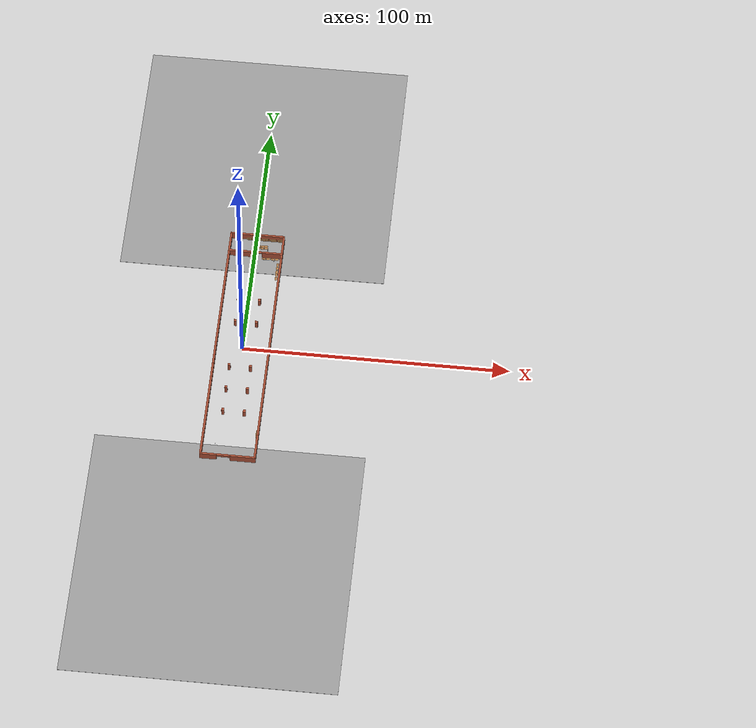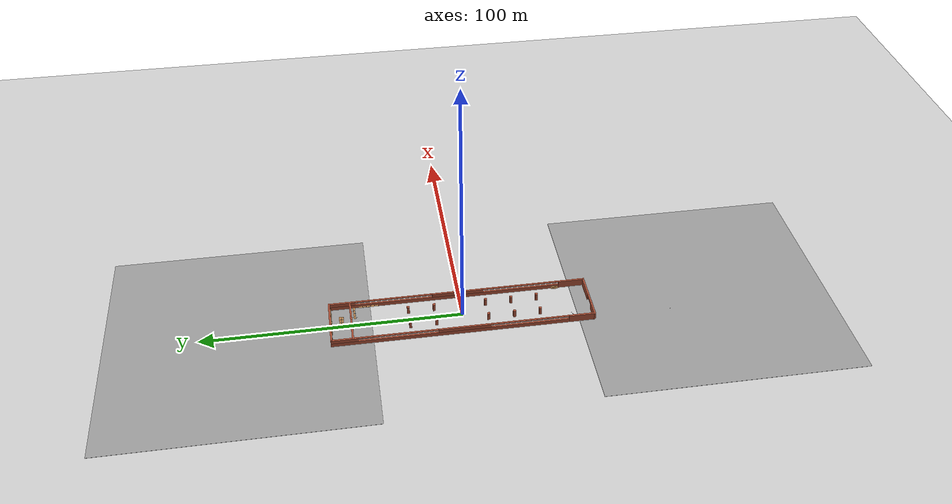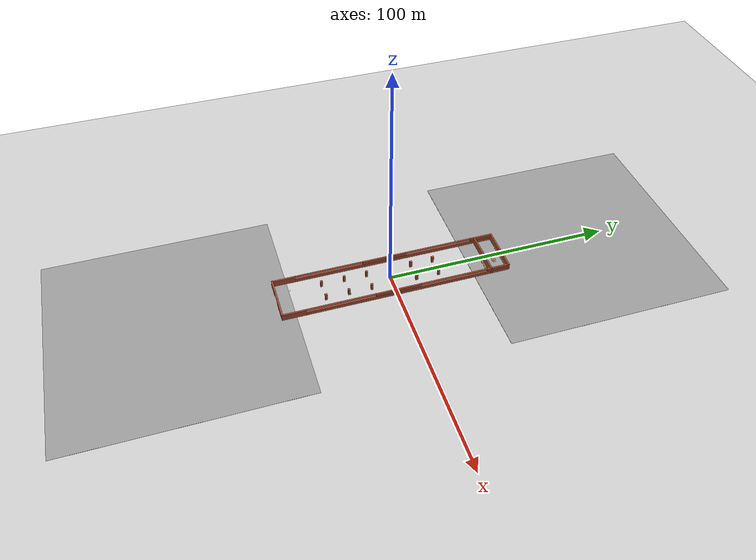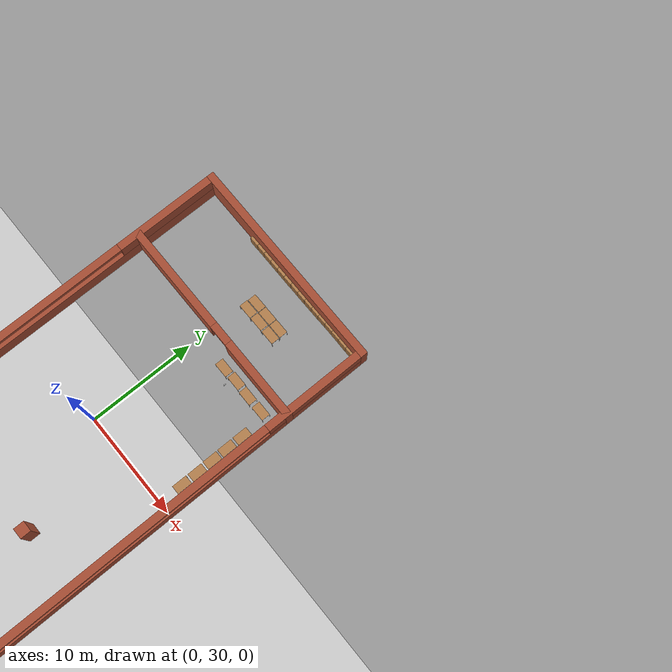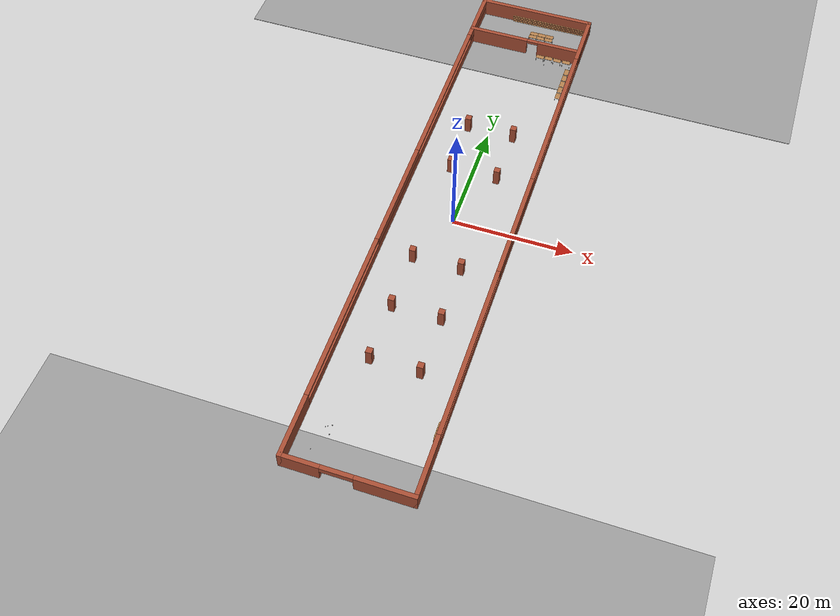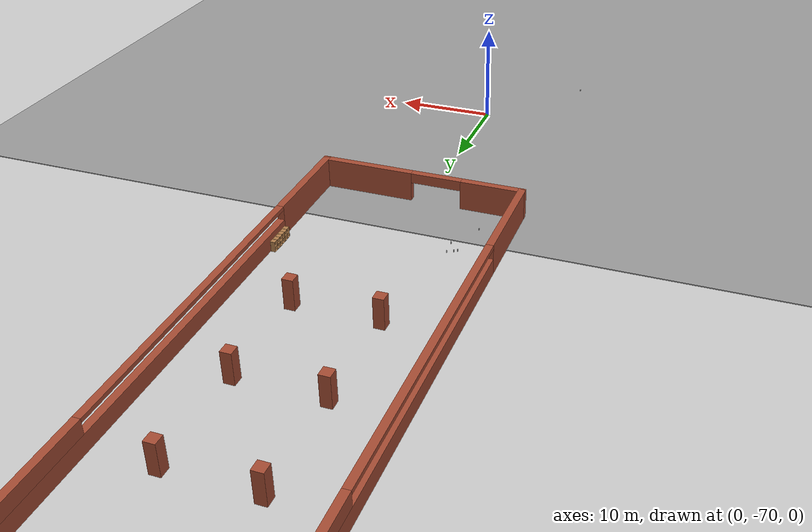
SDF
<sdf version="1.6">
 <world name="default">
  <light name="sun" type="directional">
   <pose>0 0 10 0 -0 0</pose>
   <diffuse>0.8 0.8 0.8 1</diffuse>
   <specular>0.1 0.1 0.1 1</specular>
   <attenuation>
    <range>1000</range>
    <constant>0.9</constant>
    <linear>0.01</linear>
    <quadratic>0.001</quadratic>
   </attenuation>
   <direction>-0.5 0.5 -1</direction>
  </light>
  <model name="ground_plane">
   <static>1</static>
   <link name="link">
    <collision name="collision">
     <geometry><plane><normal>0 0 1</normal><size>100 100</size></plane></geometry>
     <surface><friction><ode><mu>100</mu><mu2>50</mu2></ode></friction></surface>
    </collision>
    <visual name="visual">
     <cast_shadows>0</cast_shadows>
     <geometry><plane><normal>0 0 1</normal><size>100 100</size></plane></geometry>
     <material>
      <script><uri>file://media/materials/scripts/gazebo.material</uri><name>Gazebo/Grey</name></script>
     </material>
    </visual>
   </link>
  </model>
  <gravity>0 0 -9.8</gravity>
  <magnetic_field>6e-06 2.3e-05 -4.2e-05</magnetic_field>
  <atmosphere type="adiabatic"/>
  <physics name="default_physics" default="0" type="ode">
   <max_step_size>0.001</max_step_size>
   <real_time_factor>1</real_time_factor>
   <real_time_update_rate>1000</real_time_update_rate>
  </physics>
  <scene><ambient>0.4 0.4 0.4 1</ambient><background>0.7 0.7 0.7 1</background><shadows>1</shadows></scene>
  <spherical_coordinates>
   <surface_model>EARTH_WGS84</surface_model>
   <latitude_deg>0</latitude_deg>
   <longitude_deg>0</longitude_deg>
   <elevation>0</elevation>
   <heading_deg>0</heading_deg>
  </spherical_coordinates>
  <model name="FactoryWorldModel">
   <pose>0.257008 0.5002 0 0 -0 0</pose>
   <link name="Wall_10">
    <pose>0 -50 0 0 -0 0</pose>
    <visual name="Wall_10_Visual_0">
     <pose>-7.19666 0 1.5 0 -0 0</pose>
     <geometry><box><size>6.30668 0.7 3</size></box></geometry>
     <material>
      <script><uri>file://media/materials/scripts/gazebo.material</uri><name>Gazebo/Bricks</name></script>
      <ambient>1 1 1 1</ambient>
     </material>
    </visual>
    <collision name="Wall_10_Collision_0">
     <geometry><box><size>6.30668 0.7 3</size></box></geometry>
     <pose>-7.19666 0 1.5 0 -0 0</pose>
    </collision>
    <visual name="Wall_10_Visual_1">
     <pose>5.65334 0 1.5 0 -0 0</pose>
     <geometry><box><size>9.39332 0.7 3</size></box></geometry>
     <material>
      <script><uri>file://media/materials/scripts/gazebo.material</uri><name>Gazebo/Bricks</name></script>
      <ambient>1 1 1 1</ambient>
     </material>
    </visual>
    <collision name="Wall_10_Collision_1">
     <geometry><box><size>9.39332 0.7 3</size></box></geometry>
     <pose>5.65334 0 1.5 0 -0 0</pose>
    </collision>
    <visual name="Wall_10_Visual_2">
     <pose>-1.54332 0 2.5 0 -0 0</pose>
     <geometry><box><size>5 0.7 1</size></box></geometry>
     <material>
      <script><uri>file://media/materials/scripts/gazebo.material</uri><name>Gazebo/Bricks</name></script>
      <ambient>1 1 1 1</ambient>
     </material>
    </visual>
    <collision name="Wall_10_Collision_2">
     <geometry><box><size>5 0.7 1</size></box></geometry>
     <pose>-1.54332 0 2.5 0 -0 0</pose>
    </collision>
   </link>
   <link name="Wall_14">
    <collision name="Wall_14_Collision">
     <geometry><box><size>1 1 3</size></box></geometry>
     <pose>0 0 1.5 0 -0 0</pose>
    </collision>
    <visual name="Wall_14_Visual">
     <pose>0 0 1.5 0 -0 0</pose>
     <geometry><box><size>1 1 3</size></box></geometry>
     <material>
      <script><uri>file://media/materials/scripts/gazebo.material</uri><name>Gazebo/Bricks</name></script>
      <ambient>1 1 1 1</ambient>
     </material>
    </visual>
    <pose>4 -30 0 0 -0 0</pose>
   </link>
   <link name="Wall_16">
    <collision name="Wall_16_Collision">
     <geometry><box><size>1 1 3</size></box></geometry>
     <pose>0 0 1.5 0 -0 0</pose>
    </collision>
    <visual name="Wall_16_Visual">
     <pose>0 0 1.5 0 -0 0</pose>
     <geometry><box><size>1 1 3</size></box></geometry>
     <material>
      <script><uri>file://media/materials/scripts/gazebo.material</uri><name>Gazebo/Bricks</name></script>
      <ambient>1 1 1 1</ambient>
     </material>
    </visual>
    <pose>-4 -30 0 0 -0 0</pose>
   </link>
   <link name="Wall_18">
    <collision name="Wall_18_Collision">
     <geometry><box><size>1 1 3</size></box></geometry>
     <pose>0 0 1.5 0 -0 0</pose>
    </collision>
    <visual name="Wall_18_Visual">
     <pose>0 0 1.5 0 -0 0</pose>
     <geometry><box><size>1 1 3</size></box></geometry>
     <material>
      <script><uri>file://media/materials/scripts/gazebo.material</uri><name>Gazebo/Bricks</name></script>
      <ambient>1 1 1 1</ambient>
     </material>
    </visual>
    <pose>-4 -20 0 0 -0 0</pose>
   </link>
   <link name="Wall_2">
    <collision name="Wall_2_Collision">
     <geometry><box><size>20.7 0.7 3</size></box></geometry>
     <pose>0 0 1.5 0 -0 0</pose>
    </collision>
    <visual name="Wall_2_Visual">
     <pose>0 0 1.5 0 -0 0</pose>
     <geometry><box><size>20.7 0.7 3</size></box></geometry>
     <material>
      <script><uri>file://media/materials/scripts/gazebo.material</uri><name>Gazebo/Bricks</name></script>
      <ambient>1 1 1 1</ambient>
     </material>
    </visual>
    <pose>0 50 0 0 -0 0</pose>
   </link>
   <link name="Wall_20">
    <collision name="Wall_20_Collision">
     <geometry><box><size>1 1 3</size></box></geometry>
     <pose>0 0 1.5 0 -0 0</pose>
    </collision>
    <visual name="Wall_20_Visual">
     <pose>0 0 1.5 0 -0 0</pose>
     <geometry><box><size>1 1 3</size></box></geometry>
     <material>
      <script><uri>file://media/materials/scripts/gazebo.material</uri><name>Gazebo/Bricks</name></script>
      <ambient>1 1 1 1</ambient>
     </material>
    </visual>
    <pose>4 -20 0 0 -0 0</pose>
   </link>
   <link name="Wall_22">
    <collision name="Wall_22_Collision">
     <geometry><box><size>1 1 3</size></box></geometry>
     <pose>0 0 1.5 0 -0 0</pose>
    </collision>
    <visual name="Wall_22_Visual">
     <pose>0 0 1.5 0 -0 0</pose>
     <geometry><box><size>1 1 3</size></box></geometry>
     <material>
      <script><uri>file://media/materials/scripts/gazebo.material</uri><name>Gazebo/Bricks</name></script>
      <ambient>1 1 1 1</ambient>
     </material>
    </visual>
    <pose>-4 -10 0 0 -0 0</pose>
   </link>
   <link name="Wall_24">
    <collision name="Wall_24_Collision">
     <geometry><box><size>1 1 3</size></box></geometry>
     <pose>0 0 1.5 0 -0 0</pose>
    </collision>
    <visual name="Wall_24_Visual">
     <pose>0 0 1.5 0 -0 0</pose>
     <geometry><box><size>1 1 3</size></box></geometry>
     <material>
      <script><uri>file://media/materials/scripts/gazebo.material</uri><name>Gazebo/Bricks</name></script>
      <ambient>1 1 1 1</ambient>
     </material>
    </visual>
    <pose>4 -10 0 0 -0 0</pose>
   </link>
   <link name="Wall_26">
    <collision name="Wall_26_Collision">
     <geometry><box><size>1 1 3</size></box></geometry>
     <pose>0 0 1.5 0 -0 0</pose>
    </collision>
    <visual name="Wall_26_Visual">
     <pose>0 0 1.5 0 -0 0</pose>
     <geometry><box><size>1 1 3</size></box></geometry>
     <material>
      <script><uri>file://media/materials/scripts/gazebo.material</uri><name>Gazebo/Bricks</name></script>
      <ambient>1 1 1 1</ambient>
     </material>
    </visual>
    <pose>-4 10 0 0 -0 0</pose>
   </link>
   <link name="Wall_28">
    <collision name="Wall_28_Collision">
     <geometry><box><size>1 1 3</size></box></geometry>
     <pose>0 0 1.5 0 -0 0</pose>
    </collision>
    <visual name="Wall_28_Visual">
     <pose>0 0 1.5 0 -0 0</pose>
     <geometry><box><size>1 1 3</size></box></geometry>
     <material>
      <script><uri>file://media/materials/scripts/gazebo.material</uri><name>Gazebo/Bricks</name></script>
      <ambient>1 1 1 1</ambient>
     </material>
    </visual>
    <pose>4 10 0 0 -0 0</pose>
   </link>
   <link name="Wall_31">
    <collision name="Wall_31_Collision">
     <geometry><box><size>1 1 3</size></box></geometry>
     <pose>0 0 1.5 0 -0 0</pose>
    </collision>
    <visual name="Wall_31_Visual">
     <pose>0 0 1.5 0 -0 0</pose>
     <geometry><box><size>1 1 3</size></box></geometry>
     <material>
      <script><uri>file://media/materials/scripts/gazebo.material</uri><name>Gazebo/Bricks</name></script>
      <ambient>1 1 1 1</ambient>
     </material>
    </visual>
    <pose>4 20 0 0 -0 0</pose>
   </link>
   <link name="Wall_33">
    <collision name="Wall_33_Collision">
     <geometry><box><size>1 1 3</size></box></geometry>
     <pose>0 0 1.5 0 -0 0</pose>
    </collision>
    <visual name="Wall_33_Visual">
     <pose>0 0 1.5 0 -0 0</pose>
     <geometry><box><size>1 1 3</size></box></geometry>
     <material>
      <script><uri>file://media/materials/scripts/gazebo.material</uri><name>Gazebo/Bricks</name></script>
      <ambient>1 1 1 1</ambient>
     </material>
    </visual>
    <pose>-4 20 0 0 -0 0</pose>
   </link>
   <link name="Wall_37">
    <pose>0 42 0 0 -0 0</pose>
    <visual name="Wall_37_Visual_0">
     <pose>-4.97882 0 1.5 0 -0 0</pose>
     <geometry><box><size>10.7424 0.7 3</size></box></geometry>
     <material>
      <script><uri>file://media/materials/scripts/gazebo.material</uri><name>Gazebo/Bricks</name></script>
      <ambient>1 1 1 1</ambient>
     </material>
    </visual>
    <collision name="Wall_37_Collision_0">
     <geometry><box><size>10.7424 0.7 3</size></box></geometry>
     <pose>-4.97882 0 1.5 0 -0 0</pose>
    </collision>
    <visual name="Wall_37_Visual_1">
     <pose>6.37118 0 1.5 0 -0 0</pose>
     <geometry><box><size>7.95763 0.7 3</size></box></geometry>
     <material>
      <script><uri>file://media/materials/scripts/gazebo.material</uri><name>Gazebo/Bricks</name></script>
      <ambient>1 1 1 1</ambient>
     </material>
    </visual>
    <collision name="Wall_37_Collision_1">
     <geometry><box><size>7.95763 0.7 3</size></box></geometry>
     <pose>6.37118 0 1.5 0 -0 0</pose>
    </collision>
    <visual name="Wall_37_Visual_2">
     <pose>1.39237 0 2.75 0 -0 0</pose>
     <geometry><box><size>2 0.7 0.5</size></box></geometry>
     <material>
      <script><uri>file://media/materials/scripts/gazebo.material</uri><name>Gazebo/Bricks</name></script>
      <ambient>1 1 1 1</ambient>
     </material>
    </visual>
    <collision name="Wall_37_Collision_2">
     <geometry><box><size>2 0.7 0.5</size></box></geometry>
     <pose>1.39237 0 2.75 0 -0 0</pose>
    </collision>
   </link>
   <link name="Wall_4">
    <pose>10 0 0 0 -0 1.5708</pose>
    <visual name="Wall_4_Visual_0">
     <pose>-45.175 0 1.5 0 -0 0</pose>
     <geometry><box><size>10.35 0.7 3</size></box></geometry>
     <material>
      <script><uri>file://media/materials/scripts/gazebo.material</uri><name>Gazebo/Bricks</name></script>
      <ambient>1 1 1 1</ambient>
     </material>
    </visual>
    <collision name="Wall_4_Collision_0">
     <geometry><box><size>10.35 0.7 3</size></box></geometry>
     <pose>-45.175 0 1.5 0 -0 0</pose>
    </collision>
    <visual name="Wall_4_Visual_1">
     <pose>5.175 0 0.8 0 -0 0</pose>
     <geometry><box><size>90.35 0.7 1.6</size></box></geometry>
     <material>
      <script><uri>file://media/materials/scripts/gazebo.material</uri><name>Gazebo/Bricks</name></script>
      <ambient>1 1 1 1</ambient>
     </material>
    </visual>
    <collision name="Wall_4_Collision_1">
     <geometry><box><size>90.35 0.7 1.6</size></box></geometry>
     <pose>5.175 0 0.8 0 -0 0</pose>
    </collision>
    <visual name="Wall_4_Visual_2">
     <pose>0 0 2.3 0 -0 0</pose>
     <geometry><box><size>20 0.7 1.4</size></box></geometry>
     <material>
      <script><uri>file://media/materials/scripts/gazebo.material</uri><name>Gazebo/Bricks</name></script>
      <ambient>1 1 1 1</ambient>
     </material>
    </visual>
    <collision name="Wall_4_Collision_2">
     <geometry><box><size>20 0.7 1.4</size></box></geometry>
     <pose>0 0 2.3 0 -0 0</pose>
    </collision>
    <visual name="Wall_4_Visual_3">
     <pose>45.175 0 2.3 0 -0 0</pose>
     <geometry><box><size>10.35 0.7 1.4</size></box></geometry>
     <material>
      <script><uri>file://media/materials/scripts/gazebo.material</uri><name>Gazebo/Bricks</name></script>
      <ambient>1 1 1 1</ambient>
     </material>
    </visual>
    <collision name="Wall_4_Collision_3">
     <geometry><box><size>10.35 0.7 1.4</size></box></geometry>
     <pose>45.175 0 2.3 0 -0 0</pose>
    </collision>
    <visual name="Wall_4_Visual_4">
     <pose>-25 0 2.8 0 -0 0</pose>
     <geometry><box><size>30 0.7 0.4</size></box></geometry>
     <material>
      <script><uri>file://media/materials/scripts/gazebo.material</uri><name>Gazebo/Bricks</name></script>
      <ambient>1 1 1 1</ambient>
     </material>
    </visual>
    <collision name="Wall_4_Collision_4">
     <geometry><box><size>30 0.7 0.4</size></box></geometry>
     <pose>-25 0 2.8 0 -0 0</pose>
    </collision>
    <visual name="Wall_4_Visual_5">
     <pose>25 0 2.8 0 -0 0</pose>
     <geometry><box><size>30 0.7 0.4</size></box></geometry>
     <material>
      <script><uri>file://media/materials/scripts/gazebo.material</uri><name>Gazebo/Bricks</name></script>
      <ambient>1 1 1 1</ambient>
     </material>
    </visual>
    <collision name="Wall_4_Collision_5">
     <geometry><box><size>30 0.7 0.4</size></box></geometry>
     <pose>25 0 2.8 0 -0 0</pose>
    </collision>
   </link>
   <link name="Wall_6">
    <pose>-10 0 0 0 -0 1.5708</pose>
    <visual name="Wall_6_Visual_0">
     <pose>-45.175 0 1.5 0 -0 0</pose>
     <geometry><box><size>10.35 0.7 3</size></box></geometry>
     <material>
      <script><uri>file://media/materials/scripts/gazebo.material</uri><name>Gazebo/Bricks</name></script>
      <ambient>1 1 1 1</ambient>
     </material>
    </visual>
    <collision name="Wall_6_Collision_0">
     <geometry><box><size>10.35 0.7 3</size></box></geometry>
     <pose>-45.175 0 1.5 0 -0 0</pose>
    </collision>
    <visual name="Wall_6_Visual_1">
     <pose>5.175 0 0.8 0 -0 0</pose>
     <geometry><box><size>90.35 0.7 1.6</size></box></geometry>
     <material>
      <script><uri>file://media/materials/scripts/gazebo.material</uri><name>Gazebo/Bricks</name></script>
      <ambient>1 1 1 1</ambient>
     </material>
    </visual>
    <collision name="Wall_6_Collision_1">
     <geometry><box><size>90.35 0.7 1.6</size></box></geometry>
     <pose>5.175 0 0.8 0 -0 0</pose>
    </collision>
    <visual name="Wall_6_Visual_2">
     <pose>0 0 2.3 0 -0 0</pose>
     <geometry><box><size>20 0.7 1.4</size></box></geometry>
     <material>
      <script><uri>file://media/materials/scripts/gazebo.material</uri><name>Gazebo/Bricks</name></script>
      <ambient>1 1 1 1</ambient>
     </material>
    </visual>
    <collision name="Wall_6_Collision_2">
     <geometry><box><size>20 0.7 1.4</size></box></geometry>
     <pose>0 0 2.3 0 -0 0</pose>
    </collision>
    <visual name="Wall_6_Visual_3">
     <pose>45.175 0 2.3 0 -0 0</pose>
     <geometry><box><size>10.35 0.7 1.4</size></box></geometry>
     <material>
      <script><uri>file://media/materials/scripts/gazebo.material</uri><name>Gazebo/Bricks</name></script>
      <ambient>1 1 1 1</ambient>
     </material>
    </visual>
    <collision name="Wall_6_Collision_3">
     <geometry><box><size>10.35 0.7 1.4</size></box></geometry>
     <pose>45.175 0 2.3 0 -0 0</pose>
    </collision>
    <visual name="Wall_6_Visual_4">
     <pose>-25 0 2.8 0 -0 0</pose>
     <geometry><box><size>30 0.7 0.4</size></box></geometry>
     <material>
      <script><uri>file://media/materials/scripts/gazebo.material</uri><name>Gazebo/Bricks</name></script>
      <ambient>1 1 1 1</ambient>
     </material>
    </visual>
    <collision name="Wall_6_Collision_4">
     <geometry><box><size>30 0.7 0.4</size></box></geometry>
     <pose>-25 0 2.8 0 -0 0</pose>
    </collision>
    <visual name="Wall_6_Visual_5">
     <pose>25 0 2.8 0 -0 0</pose>
     <geometry><box><size>30 0.7 0.4</size></box></geometry>
     <material>
      <script><uri>file://media/materials/scripts/gazebo.material</uri><name>Gazebo/Bricks</name></script>
      <ambient>1 1 1 1</ambient>
     </material>
    </visual>
    <collision name="Wall_6_Collision_5">
     <geometry><box><size>30 0.7 0.4</size></box></geometry>
     <pose>25 0 2.8 0 -0 0</pose>
    </collision>
   </link>
   <static>1</static>
  </model>
  <model name="table">
   <static>0</static>
   <link name="link">
    <collision name="surface">
     <pose>0 0 1 0 -0 0</pose>
     <geometry><box><size>1.5 0.8 0.03</size></box></geometry>
     <surface><friction><ode><mu>0.6</mu><mu2>0.6</mu2></ode></friction></surface>
    </collision>
    <visual name="visual1">
     <pose>0 0 1 0 -0 0</pose>
     <geometry><box><size>1.4 0.8 0.04</size></box></geometry>
     <material>
      <script><uri>file://media/materials/scripts/gazebo.material</uri><name>Gazebo/Wood</name></script>
     </material>
    </visual>
    <collision name="front_left_leg">
     <pose>0.68 0.38 0.5 0 -0 0</pose>
     <geometry><cylinder><radius>0.02</radius><length>1</length></cylinder></geometry>
    </collision>
    <visual name="front_left_leg">
     <pose>0.68 0.38 0.5 0 -0 0</pose>
     <geometry><cylinder><radius>0.02</radius><length>1</length></cylinder></geometry>
     <material>
      <script><uri>file://media/materials/scripts/gazebo.material</uri><name>Gazebo/Grey</name></script>
     </material>
    </visual>
    <collision name="front_right_leg">
     <pose>0.68 -0.38 0.5 0 -0 0</pose>
     <geometry><cylinder><radius>0.02</radius><length>1</length></cylinder></geometry>
    </collision>
    <visual name="front_right_leg">
     <pose>0.68 -0.38 0.5 0 -0 0</pose>
     <geometry><cylinder><radius>0.02</radius><length>1</length></cylinder></geometry>
     <material>
      <script><uri>file://media/materials/scripts/gazebo.material</uri><name>Gazebo/Grey</name></script>
     </material>
    </visual>
    <collision name="back_right_leg">
     <pose>-0.68 -0.38 0.5 0 -0 0</pose>
     <geometry><cylinder><radius>0.02</radius><length>1</length></cylinder></geometry>
    </collision>
    <visual name="back_right_leg">
     <pose>-0.68 -0.38 0.5 0 -0 0</pose>
     <geometry><cylinder><radius>0.02</radius><length>1</length></cylinder></geometry>
     <material>
      <script><uri>file://media/materials/scripts/gazebo.material</uri><name>Gazebo/Grey</name></script>
     </material>
    </visual>
    <collision name="back_left_leg">
     <pose>-0.68 0.38 0.5 0 -0 0</pose>
     <geometry><cylinder><radius>0.02</radius><length>1</length></cylinder></geometry>
    </collision>
    <visual name="back_left_leg">
     <pose>-0.68 0.38 0.5 0 -0 0</pose>
     <geometry><cylinder><radius>0.02</radius><length>1</length></cylinder></geometry>
     <material>
      <script><uri>file://media/materials/scripts/gazebo.material</uri><name>Gazebo/Grey</name></script>
     </material>
    </visual>
    <inertial>
     <inertia><ixx>1</ixx><ixy>0</ixy><ixz>0</ixz><iyy>1</iyy><iyz>0</iyz><izz>1</izz></inertia>
     <mass>1</mass>
    </inertial>
   </link>
   <pose>3.6453 41.0475 -1e-06 0 -1e-06 -0.005766</pose>
  </model>
  <model name="table_clone">
   <static>0</static>
   <link name="link">
    <collision name="surface">
     <pose>0 0 1 0 -0 0</pose>
     <geometry><box><size>1.5 0.8 0.03</size></box></geometry>
     <surface><friction><ode><mu>0.6</mu><mu2>0.6</mu2></ode></friction></surface>
    </collision>
    <visual name="visual1">
     <pose>0 0 1 0 -0 0</pose>
     <geometry><box><size>1.4 0.8 0.04</size></box></geometry>
     <material>
      <script><uri>file://media/materials/scripts/gazebo.material</uri><name>Gazebo/Wood</name></script>
     </material>
    </visual>
    <collision name="front_left_leg">
     <pose>0.68 0.38 0.5 0 -0 0</pose>
     <geometry><cylinder><radius>0.02</radius><length>1</length></cylinder></geometry>
    </collision>
    <visual name="front_left_leg">
     <pose>0.68 0.38 0.5 0 -0 0</pose>
     <geometry><cylinder><radius>0.02</radius><length>1</length></cylinder></geometry>
     <material>
      <script><uri>file://media/materials/scripts/gazebo.material</uri><name>Gazebo/Grey</name></script>
     </material>
    </visual>
    <collision name="front_right_leg">
     <pose>0.68 -0.38 0.5 0 -0 0</pose>
     <geometry><cylinder><radius>0.02</radius><length>1</length></cylinder></geometry>
    </collision>
    <visual name="front_right_leg">
     <pose>0.68 -0.38 0.5 0 -0 0</pose>
     <geometry><cylinder><radius>0.02</radius><length>1</length></cylinder></geometry>
     <material>
      <script><uri>file://media/materials/scripts/gazebo.material</uri><name>Gazebo/Grey</name></script>
     </material>
    </visual>
    <collision name="back_right_leg">
     <pose>-0.68 -0.38 0.5 0 -0 0</pose>
     <geometry><cylinder><radius>0.02</radius><length>1</length></cylinder></geometry>
    </collision>
    <visual name="back_right_leg">
     <pose>-0.68 -0.38 0.5 0 -0 0</pose>
     <geometry><cylinder><radius>0.02</radius><length>1</length></cylinder></geometry>
     <material>
      <script><uri>file://media/materials/scripts/gazebo.material</uri><name>Gazebo/Grey</name></script>
     </material>
    </visual>
    <collision name="back_left_leg">
     <pose>-0.68 0.38 0.5 0 -0 0</pose>
     <geometry><cylinder><radius>0.02</radius><length>1</length></cylinder></geometry>
    </collision>
    <visual name="back_left_leg">
     <pose>-0.68 0.38 0.5 0 -0 0</pose>
     <geometry><cylinder><radius>0.02</radius><length>1</length></cylinder></geometry>
     <material>
      <script><uri>file://media/materials/scripts/gazebo.material</uri><name>Gazebo/Grey</name></script>
     </material>
    </visual>
    <inertial>
     <inertia><ixx>1</ixx><ixy>0</ixy><ixz>0</ixz><iyy>1</iyy><iyz>0</iyz><izz>1</izz></inertia>
     <mass>1</mass>
    </inertial>
   </link>
   <pose>5.18698 41.1386 -5e-06 0 -0 -0.000371</pose>
  </model>
  <model name="table_clone_0">
   <static>0</static>
   <link name="link">
    <collision name="surface">
     <pose>0 0 1 0 -0 0</pose>
     <geometry><box><size>1.5 0.8 0.03</size></box></geometry>
     <surface><friction><ode><mu>0.6</mu><mu2>0.6</mu2></ode></friction></surface>
    </collision>
    <visual name="visual1">
     <pose>0 0 1 0 -0 0</pose>
     <geometry><box><size>1.4 0.8 0.04</size></box></geometry>
     <material>
      <script><uri>file://media/materials/scripts/gazebo.material</uri><name>Gazebo/Wood</name></script>
     </material>
    </visual>
    <collision name="front_left_leg">
     <pose>0.68 0.38 0.5 0 -0 0</pose>
     <geometry><cylinder><radius>0.02</radius><length>1</length></cylinder></geometry>
    </collision>
    <visual name="front_left_leg">
     <pose>0.68 0.38 0.5 0 -0 0</pose>
     <geometry><cylinder><radius>0.02</radius><length>1</length></cylinder></geometry>
     <material>
      <script><uri>file://media/materials/scripts/gazebo.material</uri><name>Gazebo/Grey</name></script>
     </material>
    </visual>
    <collision name="front_right_leg">
     <pose>0.68 -0.38 0.5 0 -0 0</pose>
     <geometry><cylinder><radius>0.02</radius><length>1</length></cylinder></geometry>
    </collision>
    <visual name="front_right_leg">
     <pose>0.68 -0.38 0.5 0 -0 0</pose>
     <geometry><cylinder><radius>0.02</radius><length>1</length></cylinder></geometry>
     <material>
      <script><uri>file://media/materials/scripts/gazebo.material</uri><name>Gazebo/Grey</name></script>
     </material>
    </visual>
    <collision name="back_right_leg">
     <pose>-0.68 -0.38 0.5 0 -0 0</pose>
     <geometry><cylinder><radius>0.02</radius><length>1</length></cylinder></geometry>
    </collision>
    <visual name="back_right_leg">
     <pose>-0.68 -0.38 0.5 0 -0 0</pose>
     <geometry><cylinder><radius>0.02</radius><length>1</length></cylinder></geometry>
     <material>
      <script><uri>file://media/materials/scripts/gazebo.material</uri><name>Gazebo/Grey</name></script>
     </material>
    </visual>
    <collision name="back_left_leg">
     <pose>-0.68 0.38 0.5 0 -0 0</pose>
     <geometry><cylinder><radius>0.02</radius><length>1</length></cylinder></geometry>
    </collision>
    <visual name="back_left_leg">
     <pose>-0.68 0.38 0.5 0 -0 0</pose>
     <geometry><cylinder><radius>0.02</radius><length>1</length></cylinder></geometry>
     <material>
      <script><uri>file://media/materials/scripts/gazebo.material</uri><name>Gazebo/Grey</name></script>
     </material>
    </visual>
    <inertial>
     <inertia><ixx>1</ixx><ixy>0</ixy><ixz>0</ixz><iyy>1</iyy><iyz>0</iyz><izz>1</izz></inertia>
     <mass>1</mass>
    </inertial>
   </link>
   <pose>6.79594 41.0781 -1e-06 -3e-06 -0 -0.010716</pose>
  </model>
  <model name="table_clone_1">
   <static>0</static>
   <link name="link">
    <collision name="surface">
     <pose>0 0 1 0 -0 0</pose>
     <geometry><box><size>1.5 0.8 0.03</size></box></geometry>
     <surface><friction><ode><mu>0.6</mu><mu2>0.6</mu2></ode></friction></surface>
    </collision>
    <visual name="visual1">
     <pose>0 0 1 0 -0 0</pose>
     <geometry><box><size>1.4 0.8 0.04</size></box></geometry>
     <material>
      <script><uri>file://media/materials/scripts/gazebo.material</uri><name>Gazebo/Wood</name></script>
     </material>
    </visual>
    <collision name="front_left_leg">
     <pose>0.68 0.38 0.5 0 -0 0</pose>
     <geometry><cylinder><radius>0.02</radius><length>1</length></cylinder></geometry>
    </collision>
    <visual name="front_left_leg">
     <pose>0.68 0.38 0.5 0 -0 0</pose>
     <geometry><cylinder><radius>0.02</radius><length>1</length></cylinder></geometry>
     <material>
      <script><uri>file://media/materials/scripts/gazebo.material</uri><name>Gazebo/Grey</name></script>
     </material>
    </visual>
    <collision name="front_right_leg">
     <pose>0.68 -0.38 0.5 0 -0 0</pose>
     <geometry><cylinder><radius>0.02</radius><length>1</length></cylinder></geometry>
    </collision>
    <visual name="front_right_leg">
     <pose>0.68 -0.38 0.5 0 -0 0</pose>
     <geometry><cylinder><radius>0.02</radius><length>1</length></cylinder></geometry>
     <material>
      <script><uri>file://media/materials/scripts/gazebo.material</uri><name>Gazebo/Grey</name></script>
     </material>
    </visual>
    <collision name="back_right_leg">
     <pose>-0.68 -0.38 0.5 0 -0 0</pose>
     <geometry><cylinder><radius>0.02</radius><length>1</length></cylinder></geometry>
    </collision>
    <visual name="back_right_leg">
     <pose>-0.68 -0.38 0.5 0 -0 0</pose>
     <geometry><cylinder><radius>0.02</radius><length>1</length></cylinder></geometry>
     <material>
      <script><uri>file://media/materials/scripts/gazebo.material</uri><name>Gazebo/Grey</name></script>
     </material>
    </visual>
    <collision name="back_left_leg">
     <pose>-0.68 0.38 0.5 0 -0 0</pose>
     <geometry><cylinder><radius>0.02</radius><length>1</length></cylinder></geometry>
    </collision>
    <visual name="back_left_leg">
     <pose>-0.68 0.38 0.5 0 -0 0</pose>
     <geometry><cylinder><radius>0.02</radius><length>1</length></cylinder></geometry>
     <material>
      <script><uri>file://media/materials/scripts/gazebo.material</uri><name>Gazebo/Grey</name></script>
     </material>
    </visual>
    <inertial>
     <inertia><ixx>1</ixx><ixy>0</ixy><ixz>0</ixz><iyy>1</iyy><iyz>0</iyz><izz>1</izz></inertia>
     <mass>1</mass>
    </inertial>
   </link>
   <pose>8.47894 41.1162 -0 0 -0 0</pose>
  </model>
  <model name="beer">
   <link name="link">
    <pose>0 0 0.115 0 -0 0</pose>
    <inertial>
     <mass>0.39</mass>
     <inertia><ixx>0.00058</ixx><ixy>0</ixy><ixz>0</ixz><iyy>0.00058</iyy><iyz>0</iyz><izz>0.00019</izz></inertia>
    </inertial>
    <collision name="collision">
     <geometry><cylinder><radius>0.055</radius><length>0.23</length></cylinder></geometry>
    </collision>
    <visual name="visual">
     <geometry><cylinder><radius>0.055</radius><length>0.23</length></cylinder></geometry>
     <material>
      <script>
       <uri>model://beer/materials/scripts</uri>
       <uri>model://beer/materials/textures</uri>
       <name>Beer/Diffuse</name>
      </script>
     </material>
    </visual>
   </link>
   <pose>4.59629 40.137 0.054918 -1.57032 -0.739659 0.001286</pose>
  </model>
  <model name="bookshelf_clone_clone_3">
   <static>1</static>
   <link name="link">
    <inertial><mass>1</mass></inertial>
    <collision name="back">
     <pose>0 0.005 0.6 0 -0 0</pose>
     <geometry><box><size>0.9 0.01 1.2</size></box></geometry>
    </collision>
    <visual name="visual1">
     <pose>0 0.005 0.6 0 -0 0</pose>
     <geometry><box><size>0.9 0.01 1.2</size></box></geometry>
     <material>
      <script><uri>file://media/materials/scripts/gazebo.material</uri><name>Gazebo/Wood</name></script>
     </material>
    </visual>
    <collision name="left_side">
     <pose>0.45 -0.195 0.6 0 -0 0</pose>
     <geometry><box><size>0.02 0.4 1.2</size></box></geometry>
    </collision>
    <visual name="visual2">
     <pose>0.45 -0.195 0.6 0 -0 0</pose>
     <geometry><box><size>0.02 0.4 1.2</size></box></geometry>
     <material>
      <script><uri>file://media/materials/scripts/gazebo.material</uri><name>Gazebo/Wood</name></script>
     </material>
    </visual>
    <collision name="right_side">
     <pose>-0.45 -0.195 0.6 0 -0 0</pose>
     <geometry><box><size>0.02 0.4 1.2</size></box></geometry>
    </collision>
    <visual name="visual3">
     <pose>-0.45 -0.195 0.6 0 -0 0</pose>
     <geometry><box><size>0.02 0.4 1.2</size></box></geometry>
     <material>
      <script><uri>file://media/materials/scripts/gazebo.material</uri><name>Gazebo/Wood</name></script>
     </material>
    </visual>
    <collision name="bottom">
     <pose>0 -0.195 0.03 0 -0 0</pose>
     <geometry><box><size>0.88 0.4 0.06</size></box></geometry>
    </collision>
    <visual name="visual4">
     <pose>0 -0.195 0.03 0 -0 0</pose>
     <geometry><box><size>0.88 0.4 0.06</size></box></geometry>
     <material>
      <script><uri>file://media/materials/scripts/gazebo.material</uri><name>Gazebo/Wood</name></script>
     </material>
    </visual>
    <collision name="top">
     <pose>0 -0.195 1.19 0 -0 0</pose>
     <geometry><box><size>0.88 0.4 0.02</size></box></geometry>
    </collision>
    <visual name="visual5">
     <pose>0 -0.195 1.19 0 -0 0</pose>
     <geometry><box><size>0.88 0.4 0.02</size></box></geometry>
     <material>
      <script><uri>file://media/materials/scripts/gazebo.material</uri><name>Gazebo/Wood</name></script>
     </material>
    </visual>
    <collision name="low_shelf">
     <pose>0 -0.195 0.43 0 -0 0</pose>
     <geometry><box><size>0.88 0.4 0.02</size></box></geometry>
    </collision>
    <visual name="visual6">
     <pose>0 -0.195 0.43 0 -0 0</pose>
     <geometry><box><size>0.88 0.4 0.02</size></box></geometry>
     <material>
      <script><uri>file://media/materials/scripts/gazebo.material</uri><name>Gazebo/Wood</name></script>
     </material>
    </visual>
    <collision name="high_shelf">
     <pose>0 -0.195 0.8 0 -0 0</pose>
     <geometry><box><size>0.88 0.4 0.02</size></box></geometry>
    </collision>
    <visual name="visual7">
     <pose>0 -0.195 0.8 0 -0 0</pose>
     <geometry><box><size>0.88 0.4 0.02</size></box></geometry>
     <material>
      <script><uri>file://media/materials/scripts/gazebo.material</uri><name>Gazebo/Wood</name></script>
     </material>
    </visual>
   </link>
   <pose>-3.45242 50.2827 0 0 -0 0</pose>
  </model>
  <model name="bookshelf_clone_clone_4">
   <static>1</static>
   <link name="link">
    <inertial><mass>1</mass></inertial>
    <collision name="back">
     <pose>0 0.005 0.6 0 -0 0</pose>
     <geometry><box><size>0.9 0.01 1.2</size></box></geometry>
    </collision>
    <visual name="visual1">
     <pose>0 0.005 0.6 0 -0 0</pose>
     <geometry><box><size>0.9 0.01 1.2</size></box></geometry>
     <material>
      <script><uri>file://media/materials/scripts/gazebo.material</uri><name>Gazebo/Wood</name></script>
     </material>
    </visual>
    <collision name="left_side">
     <pose>0.45 -0.195 0.6 0 -0 0</pose>
     <geometry><box><size>0.02 0.4 1.2</size></box></geometry>
    </collision>
    <visual name="visual2">
     <pose>0.45 -0.195 0.6 0 -0 0</pose>
     <geometry><box><size>0.02 0.4 1.2</size></box></geometry>
     <material>
      <script><uri>file://media/materials/scripts/gazebo.material</uri><name>Gazebo/Wood</name></script>
     </material>
    </visual>
    <collision name="right_side">
     <pose>-0.45 -0.195 0.6 0 -0 0</pose>
     <geometry><box><size>0.02 0.4 1.2</size></box></geometry>
    </collision>
    <visual name="visual3">
     <pose>-0.45 -0.195 0.6 0 -0 0</pose>
     <geometry><box><size>0.02 0.4 1.2</size></box></geometry>
     <material>
      <script><uri>file://media/materials/scripts/gazebo.material</uri><name>Gazebo/Wood</name></script>
     </material>
    </visual>
    <collision name="bottom">
     <pose>0 -0.195 0.03 0 -0 0</pose>
     <geometry><box><size>0.88 0.4 0.06</size></box></geometry>
    </collision>
    <visual name="visual4">
     <pose>0 -0.195 0.03 0 -0 0</pose>
     <geometry><box><size>0.88 0.4 0.06</size></box></geometry>
     <material>
      <script><uri>file://media/materials/scripts/gazebo.material</uri><name>Gazebo/Wood</name></script>
     </material>
    </visual>
    <collision name="top">
     <pose>0 -0.195 1.19 0 -0 0</pose>
     <geometry><box><size>0.88 0.4 0.02</size></box></geometry>
    </collision>
    <visual name="visual5">
     <pose>0 -0.195 1.19 0 -0 0</pose>
     <geometry><box><size>0.88 0.4 0.02</size></box></geometry>
     <material>
      <script><uri>file://media/materials/scripts/gazebo.material</uri><name>Gazebo/Wood</name></script>
     </material>
    </visual>
    <collision name="low_shelf">
     <pose>0 -0.195 0.43 0 -0 0</pose>
     <geometry><box><size>0.88 0.4 0.02</size></box></geometry>
    </collision>
    <visual name="visual6">
     <pose>0 -0.195 0.43 0 -0 0</pose>
     <geometry><box><size>0.88 0.4 0.02</size></box></geometry>
     <material>
      <script><uri>file://media/materials/scripts/gazebo.material</uri><name>Gazebo/Wood</name></script>
     </material>
    </visual>
    <collision name="high_shelf">
     <pose>0 -0.195 0.8 0 -0 0</pose>
     <geometry><box><size>0.88 0.4 0.02</size></box></geometry>
    </collision>
    <visual name="visual7">
     <pose>0 -0.195 0.8 0 -0 0</pose>
     <geometry><box><size>0.88 0.4 0.02</size></box></geometry>
     <material>
      <script><uri>file://media/materials/scripts/gazebo.material</uri><name>Gazebo/Wood</name></script>
     </material>
    </visual>
   </link>
   <pose>-2.53043 50.2921 0 0 -0 0</pose>
  </model>
  <model name="bookshelf_clone_clone_5">
   <static>1</static>
   <link name="link">
    <inertial><mass>1</mass></inertial>
    <collision name="back">
     <pose>0 0.005 0.6 0 -0 0</pose>
     <geometry><box><size>0.9 0.01 1.2</size></box></geometry>
    </collision>
    <visual name="visual1">
     <pose>0 0.005 0.6 0 -0 0</pose>
     <geometry><box><size>0.9 0.01 1.2</size></box></geometry>
     <material>
      <script><uri>file://media/materials/scripts/gazebo.material</uri><name>Gazebo/Wood</name></script>
     </material>
    </visual>
    <collision name="left_side">
     <pose>0.45 -0.195 0.6 0 -0 0</pose>
     <geometry><box><size>0.02 0.4 1.2</size></box></geometry>
    </collision>
    <visual name="visual2">
     <pose>0.45 -0.195 0.6 0 -0 0</pose>
     <geometry><box><size>0.02 0.4 1.2</size></box></geometry>
     <material>
      <script><uri>file://media/materials/scripts/gazebo.material</uri><name>Gazebo/Wood</name></script>
     </material>
    </visual>
    <collision name="right_side">
     <pose>-0.45 -0.195 0.6 0 -0 0</pose>
     <geometry><box><size>0.02 0.4 1.2</size></box></geometry>
    </collision>
    <visual name="visual3">
     <pose>-0.45 -0.195 0.6 0 -0 0</pose>
     <geometry><box><size>0.02 0.4 1.2</size></box></geometry>
     <material>
      <script><uri>file://media/materials/scripts/gazebo.material</uri><name>Gazebo/Wood</name></script>
     </material>
    </visual>
    <collision name="bottom">
     <pose>0 -0.195 0.03 0 -0 0</pose>
     <geometry><box><size>0.88 0.4 0.06</size></box></geometry>
    </collision>
    <visual name="visual4">
     <pose>0 -0.195 0.03 0 -0 0</pose>
     <geometry><box><size>0.88 0.4 0.06</size></box></geometry>
     <material>
      <script><uri>file://media/materials/scripts/gazebo.material</uri><name>Gazebo/Wood</name></script>
     </material>
    </visual>
    <collision name="top">
     <pose>0 -0.195 1.19 0 -0 0</pose>
     <geometry><box><size>0.88 0.4 0.02</size></box></geometry>
    </collision>
    <visual name="visual5">
     <pose>0 -0.195 1.19 0 -0 0</pose>
     <geometry><box><size>0.88 0.4 0.02</size></box></geometry>
     <material>
      <script><uri>file://media/materials/scripts/gazebo.material</uri><name>Gazebo/Wood</name></script>
     </material>
    </visual>
    <collision name="low_shelf">
     <pose>0 -0.195 0.43 0 -0 0</pose>
     <geometry><box><size>0.88 0.4 0.02</size></box></geometry>
    </collision>
    <visual name="visual6">
     <pose>0 -0.195 0.43 0 -0 0</pose>
     <geometry><box><size>0.88 0.4 0.02</size></box></geometry>
     <material>
      <script><uri>file://media/materials/scripts/gazebo.material</uri><name>Gazebo/Wood</name></script>
     </material>
    </visual>
    <collision name="high_shelf">
     <pose>0 -0.195 0.8 0 -0 0</pose>
     <geometry><box><size>0.88 0.4 0.02</size></box></geometry>
    </collision>
    <visual name="visual7">
     <pose>0 -0.195 0.8 0 -0 0</pose>
     <geometry><box><size>0.88 0.4 0.02</size></box></geometry>
     <material>
      <script><uri>file://media/materials/scripts/gazebo.material</uri><name>Gazebo/Wood</name></script>
     </material>
    </visual>
   </link>
   <pose>-1.60843 50.2898 0 0 -0 0</pose>
  </model>
  <model name="bookshelf_clone_clone_6">
   <static>1</static>
   <link name="link">
    <inertial><mass>1</mass></inertial>
    <collision name="back">
     <pose>0 0.005 0.6 0 -0 0</pose>
     <geometry><box><size>0.9 0.01 1.2</size></box></geometry>
    </collision>
    <visual name="visual1">
     <pose>0 0.005 0.6 0 -0 0</pose>
     <geometry><box><size>0.9 0.01 1.2</size></box></geometry>
     <material>
      <script><uri>file://media/materials/scripts/gazebo.material</uri><name>Gazebo/Wood</name></script>
     </material>
    </visual>
    <collision name="left_side">
     <pose>0.45 -0.195 0.6 0 -0 0</pose>
     <geometry><box><size>0.02 0.4 1.2</size></box></geometry>
    </collision>
    <visual name="visual2">
     <pose>0.45 -0.195 0.6 0 -0 0</pose>
     <geometry><box><size>0.02 0.4 1.2</size></box></geometry>
     <material>
      <script><uri>file://media/materials/scripts/gazebo.material</uri><name>Gazebo/Wood</name></script>
     </material>
    </visual>
    <collision name="right_side">
     <pose>-0.45 -0.195 0.6 0 -0 0</pose>
     <geometry><box><size>0.02 0.4 1.2</size></box></geometry>
    </collision>
    <visual name="visual3">
     <pose>-0.45 -0.195 0.6 0 -0 0</pose>
     <geometry><box><size>0.02 0.4 1.2</size></box></geometry>
     <material>
      <script><uri>file://media/materials/scripts/gazebo.material</uri><name>Gazebo/Wood</name></script>
     </material>
    </visual>
    <collision name="bottom">
     <pose>0 -0.195 0.03 0 -0 0</pose>
     <geometry><box><size>0.88 0.4 0.06</size></box></geometry>
    </collision>
    <visual name="visual4">
     <pose>0 -0.195 0.03 0 -0 0</pose>
     <geometry><box><size>0.88 0.4 0.06</size></box></geometry>
     <material>
      <script><uri>file://media/materials/scripts/gazebo.material</uri><name>Gazebo/Wood</name></script>
     </material>
    </visual>
    <collision name="top">
     <pose>0 -0.195 1.19 0 -0 0</pose>
     <geometry><box><size>0.88 0.4 0.02</size></box></geometry>
    </collision>
    <visual name="visual5">
     <pose>0 -0.195 1.19 0 -0 0</pose>
     <geometry><box><size>0.88 0.4 0.02</size></box></geometry>
     <material>
      <script><uri>file://media/materials/scripts/gazebo.material</uri><name>Gazebo/Wood</name></script>
     </material>
    </visual>
    <collision name="low_shelf">
     <pose>0 -0.195 0.43 0 -0 0</pose>
     <geometry><box><size>0.88 0.4 0.02</size></box></geometry>
    </collision>
    <visual name="visual6">
     <pose>0 -0.195 0.43 0 -0 0</pose>
     <geometry><box><size>0.88 0.4 0.02</size></box></geometry>
     <material>
      <script><uri>file://media/materials/scripts/gazebo.material</uri><name>Gazebo/Wood</name></script>
     </material>
    </visual>
    <collision name="high_shelf">
     <pose>0 -0.195 0.8 0 -0 0</pose>
     <geometry><box><size>0.88 0.4 0.02</size></box></geometry>
    </collision>
    <visual name="visual7">
     <pose>0 -0.195 0.8 0 -0 0</pose>
     <geometry><box><size>0.88 0.4 0.02</size></box></geometry>
     <material>
      <script><uri>file://media/materials/scripts/gazebo.material</uri><name>Gazebo/Wood</name></script>
     </material>
    </visual>
   </link>
   <pose>-0.705048 50.2874 0 0 -0 0</pose>
  </model>
  <model name="bookshelf_clone_clone_7">
   <static>1</static>
   <link name="link">
    <inertial><mass>1</mass></inertial>
    <collision name="back">
     <pose>0 0.005 0.6 0 -0 0</pose>
     <geometry><box><size>0.9 0.01 1.2</size></box></geometry>
    </collision>
    <visual name="visual1">
     <pose>0 0.005 0.6 0 -0 0</pose>
     <geometry><box><size>0.9 0.01 1.2</size></box></geometry>
     <material>
      <script><uri>file://media/materials/scripts/gazebo.material</uri><name>Gazebo/Wood</name></script>
     </material>
    </visual>
    <collision name="left_side">
     <pose>0.45 -0.195 0.6 0 -0 0</pose>
     <geometry><box><size>0.02 0.4 1.2</size></box></geometry>
    </collision>
    <visual name="visual2">
     <pose>0.45 -0.195 0.6 0 -0 0</pose>
     <geometry><box><size>0.02 0.4 1.2</size></box></geometry>
     <material>
      <script><uri>file://media/materials/scripts/gazebo.material</uri><name>Gazebo/Wood</name></script>
     </material>
    </visual>
    <collision name="right_side">
     <pose>-0.45 -0.195 0.6 0 -0 0</pose>
     <geometry><box><size>0.02 0.4 1.2</size></box></geometry>
    </collision>
    <visual name="visual3">
     <pose>-0.45 -0.195 0.6 0 -0 0</pose>
     <geometry><box><size>0.02 0.4 1.2</size></box></geometry>
     <material>
      <script><uri>file://media/materials/scripts/gazebo.material</uri><name>Gazebo/Wood</name></script>
     </material>
    </visual>
    <collision name="bottom">
     <pose>0 -0.195 0.03 0 -0 0</pose>
     <geometry><box><size>0.88 0.4 0.06</size></box></geometry>
    </collision>
    <visual name="visual4">
     <pose>0 -0.195 0.03 0 -0 0</pose>
     <geometry><box><size>0.88 0.4 0.06</size></box></geometry>
     <material>
      <script><uri>file://media/materials/scripts/gazebo.material</uri><name>Gazebo/Wood</name></script>
     </material>
    </visual>
    <collision name="top">
     <pose>0 -0.195 1.19 0 -0 0</pose>
     <geometry><box><size>0.88 0.4 0.02</size></box></geometry>
    </collision>
    <visual name="visual5">
     <pose>0 -0.195 1.19 0 -0 0</pose>
     <geometry><box><size>0.88 0.4 0.02</size></box></geometry>
     <material>
      <script><uri>file://media/materials/scripts/gazebo.material</uri><name>Gazebo/Wood</name></script>
     </material>
    </visual>
    <collision name="low_shelf">
     <pose>0 -0.195 0.43 0 -0 0</pose>
     <geometry><box><size>0.88 0.4 0.02</size></box></geometry>
    </collision>
    <visual name="visual6">
     <pose>0 -0.195 0.43 0 -0 0</pose>
     <geometry><box><size>0.88 0.4 0.02</size></box></geometry>
     <material>
      <script><uri>file://media/materials/scripts/gazebo.material</uri><name>Gazebo/Wood</name></script>
     </material>
    </visual>
    <collision name="high_shelf">
     <pose>0 -0.195 0.8 0 -0 0</pose>
     <geometry><box><size>0.88 0.4 0.02</size></box></geometry>
    </collision>
    <visual name="visual7">
     <pose>0 -0.195 0.8 0 -0 0</pose>
     <geometry><box><size>0.88 0.4 0.02</size></box></geometry>
     <material>
      <script><uri>file://media/materials/scripts/gazebo.material</uri><name>Gazebo/Wood</name></script>
     </material>
    </visual>
   </link>
   <pose>0.208745 50.2879 0 0 -0 0</pose>
  </model>
  <model name="bookshelf_clone_clone_8">
   <static>1</static>
   <link name="link">
    <inertial><mass>1</mass></inertial>
    <collision name="back">
     <pose>0 0.005 0.6 0 -0 0</pose>
     <geometry><box><size>0.9 0.01 1.2</size></box></geometry>
    </collision>
    <visual name="visual1">
     <pose>0 0.005 0.6 0 -0 0</pose>
     <geometry><box><size>0.9 0.01 1.2</size></box></geometry>
     <material>
      <script><uri>file://media/materials/scripts/gazebo.material</uri><name>Gazebo/Wood</name></script>
     </material>
    </visual>
    <collision name="left_side">
     <pose>0.45 -0.195 0.6 0 -0 0</pose>
     <geometry><box><size>0.02 0.4 1.2</size></box></geometry>
    </collision>
    <visual name="visual2">
     <pose>0.45 -0.195 0.6 0 -0 0</pose>
     <geometry><box><size>0.02 0.4 1.2</size></box></geometry>
     <material>
      <script><uri>file://media/materials/scripts/gazebo.material</uri><name>Gazebo/Wood</name></script>
     </material>
    </visual>
    <collision name="right_side">
     <pose>-0.45 -0.195 0.6 0 -0 0</pose>
     <geometry><box><size>0.02 0.4 1.2</size></box></geometry>
    </collision>
    <visual name="visual3">
     <pose>-0.45 -0.195 0.6 0 -0 0</pose>
     <geometry><box><size>0.02 0.4 1.2</size></box></geometry>
     <material>
      <script><uri>file://media/materials/scripts/gazebo.material</uri><name>Gazebo/Wood</name></script>
     </material>
    </visual>
    <collision name="bottom">
     <pose>0 -0.195 0.03 0 -0 0</pose>
     <geometry><box><size>0.88 0.4 0.06</size></box></geometry>
    </collision>
    <visual name="visual4">
     <pose>0 -0.195 0.03 0 -0 0</pose>
     <geometry><box><size>0.88 0.4 0.06</size></box></geometry>
     <material>
      <script><uri>file://media/materials/scripts/gazebo.material</uri><name>Gazebo/Wood</name></script>
     </material>
    </visual>
    <collision name="top">
     <pose>0 -0.195 1.19 0 -0 0</pose>
     <geometry><box><size>0.88 0.4 0.02</size></box></geometry>
    </collision>
    <visual name="visual5">
     <pose>0 -0.195 1.19 0 -0 0</pose>
     <geometry><box><size>0.88 0.4 0.02</size></box></geometry>
     <material>
      <script><uri>file://media/materials/scripts/gazebo.material</uri><name>Gazebo/Wood</name></script>
     </material>
    </visual>
    <collision name="low_shelf">
     <pose>0 -0.195 0.43 0 -0 0</pose>
     <geometry><box><size>0.88 0.4 0.02</size></box></geometry>
    </collision>
    <visual name="visual6">
     <pose>0 -0.195 0.43 0 -0 0</pose>
     <geometry><box><size>0.88 0.4 0.02</size></box></geometry>
     <material>
      <script><uri>file://media/materials/scripts/gazebo.material</uri><name>Gazebo/Wood</name></script>
     </material>
    </visual>
    <collision name="high_shelf">
     <pose>0 -0.195 0.8 0 -0 0</pose>
     <geometry><box><size>0.88 0.4 0.02</size></box></geometry>
    </collision>
    <visual name="visual7">
     <pose>0 -0.195 0.8 0 -0 0</pose>
     <geometry><box><size>0.88 0.4 0.02</size></box></geometry>
     <material>
      <script><uri>file://media/materials/scripts/gazebo.material</uri><name>Gazebo/Wood</name></script>
     </material>
    </visual>
   </link>
   <pose>1.1123 50.2856 0 0 -0 0</pose>
  </model>
  <model name="bookshelf_clone_clone_9">
   <static>1</static>
   <link name="link">
    <inertial><mass>1</mass></inertial>
    <collision name="back">
     <pose>0 0.005 0.6 0 -0 0</pose>
     <geometry><box><size>0.9 0.01 1.2</size></box></geometry>
    </collision>
    <visual name="visual1">
     <pose>0 0.005 0.6 0 -0 0</pose>
     <geometry><box><size>0.9 0.01 1.2</size></box></geometry>
     <material>
      <script><uri>file://media/materials/scripts/gazebo.material</uri><name>Gazebo/Wood</name></script>
     </material>
    </visual>
    <collision name="left_side">
     <pose>0.45 -0.195 0.6 0 -0 0</pose>
     <geometry><box><size>0.02 0.4 1.2</size></box></geometry>
    </collision>
    <visual name="visual2">
     <pose>0.45 -0.195 0.6 0 -0 0</pose>
     <geometry><box><size>0.02 0.4 1.2</size></box></geometry>
     <material>
      <script><uri>file://media/materials/scripts/gazebo.material</uri><name>Gazebo/Wood</name></script>
     </material>
    </visual>
    <collision name="right_side">
     <pose>-0.45 -0.195 0.6 0 -0 0</pose>
     <geometry><box><size>0.02 0.4 1.2</size></box></geometry>
    </collision>
    <visual name="visual3">
     <pose>-0.45 -0.195 0.6 0 -0 0</pose>
     <geometry><box><size>0.02 0.4 1.2</size></box></geometry>
     <material>
      <script><uri>file://media/materials/scripts/gazebo.material</uri><name>Gazebo/Wood</name></script>
     </material>
    </visual>
    <collision name="bottom">
     <pose>0 -0.195 0.03 0 -0 0</pose>
     <geometry><box><size>0.88 0.4 0.06</size></box></geometry>
    </collision>
    <visual name="visual4">
     <pose>0 -0.195 0.03 0 -0 0</pose>
     <geometry><box><size>0.88 0.4 0.06</size></box></geometry>
     <material>
      <script><uri>file://media/materials/scripts/gazebo.material</uri><name>Gazebo/Wood</name></script>
     </material>
    </visual>
    <collision name="top">
     <pose>0 -0.195 1.19 0 -0 0</pose>
     <geometry><box><size>0.88 0.4 0.02</size></box></geometry>
    </collision>
    <visual name="visual5">
     <pose>0 -0.195 1.19 0 -0 0</pose>
     <geometry><box><size>0.88 0.4 0.02</size></box></geometry>
     <material>
      <script><uri>file://media/materials/scripts/gazebo.material</uri><name>Gazebo/Wood</name></script>
     </material>
    </visual>
    <collision name="low_shelf">
     <pose>0 -0.195 0.43 0 -0 0</pose>
     <geometry><box><size>0.88 0.4 0.02</size></box></geometry>
    </collision>
    <visual name="visual6">
     <pose>0 -0.195 0.43 0 -0 0</pose>
     <geometry><box><size>0.88 0.4 0.02</size></box></geometry>
     <material>
      <script><uri>file://media/materials/scripts/gazebo.material</uri><name>Gazebo/Wood</name></script>
     </material>
    </visual>
    <collision name="high_shelf">
     <pose>0 -0.195 0.8 0 -0 0</pose>
     <geometry><box><size>0.88 0.4 0.02</size></box></geometry>
    </collision>
    <visual name="visual7">
     <pose>0 -0.195 0.8 0 -0 0</pose>
     <geometry><box><size>0.88 0.4 0.02</size></box></geometry>
     <material>
      <script><uri>file://media/materials/scripts/gazebo.material</uri><name>Gazebo/Wood</name></script>
     </material>
    </visual>
   </link>
   <pose>2.03547 50.2951 0 0 -0 0</pose>
  </model>
  <model name="bookshelf_clone_clone_10">
   <static>1</static>
   <link name="link">
    <inertial><mass>1</mass></inertial>
    <collision name="back">
     <pose>0 0.005 0.6 0 -0 0</pose>
     <geometry><box><size>0.9 0.01 1.2</size></box></geometry>
    </collision>
    <visual name="visual1">
     <pose>0 0.005 0.6 0 -0 0</pose>
     <geometry><box><size>0.9 0.01 1.2</size></box></geometry>
     <material>
      <script><uri>file://media/materials/scripts/gazebo.material</uri><name>Gazebo/Wood</name></script>
     </material>
    </visual>
    <collision name="left_side">
     <pose>0.45 -0.195 0.6 0 -0 0</pose>
     <geometry><box><size>0.02 0.4 1.2</size></box></geometry>
    </collision>
    <visual name="visual2">
     <pose>0.45 -0.195 0.6 0 -0 0</pose>
     <geometry><box><size>0.02 0.4 1.2</size></box></geometry>
     <material>
      <script><uri>file://media/materials/scripts/gazebo.material</uri><name>Gazebo/Wood</name></script>
     </material>
    </visual>
    <collision name="right_side">
     <pose>-0.45 -0.195 0.6 0 -0 0</pose>
     <geometry><box><size>0.02 0.4 1.2</size></box></geometry>
    </collision>
    <visual name="visual3">
     <pose>-0.45 -0.195 0.6 0 -0 0</pose>
     <geometry><box><size>0.02 0.4 1.2</size></box></geometry>
     <material>
      <script><uri>file://media/materials/scripts/gazebo.material</uri><name>Gazebo/Wood</name></script>
     </material>
    </visual>
    <collision name="bottom">
     <pose>0 -0.195 0.03 0 -0 0</pose>
     <geometry><box><size>0.88 0.4 0.06</size></box></geometry>
    </collision>
    <visual name="visual4">
     <pose>0 -0.195 0.03 0 -0 0</pose>
     <geometry><box><size>0.88 0.4 0.06</size></box></geometry>
     <material>
      <script><uri>file://media/materials/scripts/gazebo.material</uri><name>Gazebo/Wood</name></script>
     </material>
    </visual>
    <collision name="top">
     <pose>0 -0.195 1.19 0 -0 0</pose>
     <geometry><box><size>0.88 0.4 0.02</size></box></geometry>
    </collision>
    <visual name="visual5">
     <pose>0 -0.195 1.19 0 -0 0</pose>
     <geometry><box><size>0.88 0.4 0.02</size></box></geometry>
     <material>
      <script><uri>file://media/materials/scripts/gazebo.material</uri><name>Gazebo/Wood</name></script>
     </material>
    </visual>
    <collision name="low_shelf">
     <pose>0 -0.195 0.43 0 -0 0</pose>
     <geometry><box><size>0.88 0.4 0.02</size></box></geometry>
    </collision>
    <visual name="visual6">
     <pose>0 -0.195 0.43 0 -0 0</pose>
     <geometry><box><size>0.88 0.4 0.02</size></box></geometry>
     <material>
      <script><uri>file://media/materials/scripts/gazebo.material</uri><name>Gazebo/Wood</name></script>
     </material>
    </visual>
    <collision name="high_shelf">
     <pose>0 -0.195 0.8 0 -0 0</pose>
     <geometry><box><size>0.88 0.4 0.02</size></box></geometry>
    </collision>
    <visual name="visual7">
     <pose>0 -0.195 0.8 0 -0 0</pose>
     <geometry><box><size>0.88 0.4 0.02</size></box></geometry>
     <material>
      <script><uri>file://media/materials/scripts/gazebo.material</uri><name>Gazebo/Wood</name></script>
     </material>
    </visual>
   </link>
   <pose>2.94899 50.2925 0 0 -0 0</pose>
  </model>
  <model name="bookshelf_clone_clone_11">
   <static>1</static>
   <link name="link">
    <inertial><mass>1</mass></inertial>
    <collision name="back">
     <pose>0 0.005 0.6 0 -0 0</pose>
     <geometry><box><size>0.9 0.01 1.2</size></box></geometry>
    </collision>
    <visual name="visual1">
     <pose>0 0.005 0.6 0 -0 0</pose>
     <geometry><box><size>0.9 0.01 1.2</size></box></geometry>
     <material>
      <script><uri>file://media/materials/scripts/gazebo.material</uri><name>Gazebo/Wood</name></script>
     </material>
    </visual>
    <collision name="left_side">
     <pose>0.45 -0.195 0.6 0 -0 0</pose>
     <geometry><box><size>0.02 0.4 1.2</size></box></geometry>
    </collision>
    <visual name="visual2">
     <pose>0.45 -0.195 0.6 0 -0 0</pose>
     <geometry><box><size>0.02 0.4 1.2</size></box></geometry>
     <material>
      <script><uri>file://media/materials/scripts/gazebo.material</uri><name>Gazebo/Wood</name></script>
     </material>
    </visual>
    <collision name="right_side">
     <pose>-0.45 -0.195 0.6 0 -0 0</pose>
     <geometry><box><size>0.02 0.4 1.2</size></box></geometry>
    </collision>
    <visual name="visual3">
     <pose>-0.45 -0.195 0.6 0 -0 0</pose>
     <geometry><box><size>0.02 0.4 1.2</size></box></geometry>
     <material>
      <script><uri>file://media/materials/scripts/gazebo.material</uri><name>Gazebo/Wood</name></script>
     </material>
    </visual>
    <collision name="bottom">
     <pose>0 -0.195 0.03 0 -0 0</pose>
     <geometry><box><size>0.88 0.4 0.06</size></box></geometry>
    </collision>
    <visual name="visual4">
     <pose>0 -0.195 0.03 0 -0 0</pose>
     <geometry><box><size>0.88 0.4 0.06</size></box></geometry>
     <material>
      <script><uri>file://media/materials/scripts/gazebo.material</uri><name>Gazebo/Wood</name></script>
     </material>
    </visual>
    <collision name="top">
     <pose>0 -0.195 1.19 0 -0 0</pose>
     <geometry><box><size>0.88 0.4 0.02</size></box></geometry>
    </collision>
    <visual name="visual5">
     <pose>0 -0.195 1.19 0 -0 0</pose>
     <geometry><box><size>0.88 0.4 0.02</size></box></geometry>
     <material>
      <script><uri>file://media/materials/scripts/gazebo.material</uri><name>Gazebo/Wood</name></script>
     </material>
    </visual>
    <collision name="low_shelf">
     <pose>0 -0.195 0.43 0 -0 0</pose>
     <geometry><box><size>0.88 0.4 0.02</size></box></geometry>
    </collision>
    <visual name="visual6">
     <pose>0 -0.195 0.43 0 -0 0</pose>
     <geometry><box><size>0.88 0.4 0.02</size></box></geometry>
     <material>
      <script><uri>file://media/materials/scripts/gazebo.material</uri><name>Gazebo/Wood</name></script>
     </material>
    </visual>
    <collision name="high_shelf">
     <pose>0 -0.195 0.8 0 -0 0</pose>
     <geometry><box><size>0.88 0.4 0.02</size></box></geometry>
    </collision>
    <visual name="visual7">
     <pose>0 -0.195 0.8 0 -0 0</pose>
     <geometry><box><size>0.88 0.4 0.02</size></box></geometry>
     <material>
      <script><uri>file://media/materials/scripts/gazebo.material</uri><name>Gazebo/Wood</name></script>
     </material>
    </visual>
   </link>
   <pose>3.86479 50.3016 0 0 -0 0</pose>
  </model>
  <model name="bookshelf_clone_clone_12">
   <static>1</static>
   <link name="link">
    <inertial><mass>1</mass></inertial>
    <collision name="back">
     <pose>0 0.005 0.6 0 -0 0</pose>
     <geometry><box><size>0.9 0.01 1.2</size></box></geometry>
    </collision>
    <visual name="visual1">
     <pose>0 0.005 0.6 0 -0 0</pose>
     <geometry><box><size>0.9 0.01 1.2</size></box></geometry>
     <material>
      <script><uri>file://media/materials/scripts/gazebo.material</uri><name>Gazebo/Wood</name></script>
     </material>
    </visual>
    <collision name="left_side">
     <pose>0.45 -0.195 0.6 0 -0 0</pose>
     <geometry><box><size>0.02 0.4 1.2</size></box></geometry>
    </collision>
    <visual name="visual2">
     <pose>0.45 -0.195 0.6 0 -0 0</pose>
     <geometry><box><size>0.02 0.4 1.2</size></box></geometry>
     <material>
      <script><uri>file://media/materials/scripts/gazebo.material</uri><name>Gazebo/Wood</name></script>
     </material>
    </visual>
    <collision name="right_side">
     <pose>-0.45 -0.195 0.6 0 -0 0</pose>
     <geometry><box><size>0.02 0.4 1.2</size></box></geometry>
    </collision>
    <visual name="visual3">
     <pose>-0.45 -0.195 0.6 0 -0 0</pose>
     <geometry><box><size>0.02 0.4 1.2</size></box></geometry>
     <material>
      <script><uri>file://media/materials/scripts/gazebo.material</uri><name>Gazebo/Wood</name></script>
     </material>
    </visual>
    <collision name="bottom">
     <pose>0 -0.195 0.03 0 -0 0</pose>
     <geometry><box><size>0.88 0.4 0.06</size></box></geometry>
    </collision>
    <visual name="visual4">
     <pose>0 -0.195 0.03 0 -0 0</pose>
     <geometry><box><size>0.88 0.4 0.06</size></box></geometry>
     <material>
      <script><uri>file://media/materials/scripts/gazebo.material</uri><name>Gazebo/Wood</name></script>
     </material>
    </visual>
    <collision name="top">
     <pose>0 -0.195 1.19 0 -0 0</pose>
     <geometry><box><size>0.88 0.4 0.02</size></box></geometry>
    </collision>
    <visual name="visual5">
     <pose>0 -0.195 1.19 0 -0 0</pose>
     <geometry><box><size>0.88 0.4 0.02</size></box></geometry>
     <material>
      <script><uri>file://media/materials/scripts/gazebo.material</uri><name>Gazebo/Wood</name></script>
     </material>
    </visual>
    <collision name="low_shelf">
     <pose>0 -0.195 0.43 0 -0 0</pose>
     <geometry><box><size>0.88 0.4 0.02</size></box></geometry>
    </collision>
    <visual name="visual6">
     <pose>0 -0.195 0.43 0 -0 0</pose>
     <geometry><box><size>0.88 0.4 0.02</size></box></geometry>
     <material>
      <script><uri>file://media/materials/scripts/gazebo.material</uri><name>Gazebo/Wood</name></script>
     </material>
    </visual>
    <collision name="high_shelf">
     <pose>0 -0.195 0.8 0 -0 0</pose>
     <geometry><box><size>0.88 0.4 0.02</size></box></geometry>
    </collision>
    <visual name="visual7">
     <pose>0 -0.195 0.8 0 -0 0</pose>
     <geometry><box><size>0.88 0.4 0.02</size></box></geometry>
     <material>
      <script><uri>file://media/materials/scripts/gazebo.material</uri><name>Gazebo/Wood</name></script>
     </material>
    </visual>
   </link>
   <pose>4.76824 50.3098 0 0 -0 0</pose>
  </model>
  <model name="bookshelf_clone_clone_13">
   <static>1</static>
   <link name="link">
    <inertial><mass>1</mass></inertial>
    <collision name="back">
     <pose>0 0.005 0.6 0 -0 0</pose>
     <geometry><box><size>0.9 0.01 1.2</size></box></geometry>
    </collision>
    <visual name="visual1">
     <pose>0 0.005 0.6 0 -0 0</pose>
     <geometry><box><size>0.9 0.01 1.2</size></box></geometry>
     <material>
      <script><uri>file://media/materials/scripts/gazebo.material</uri><name>Gazebo/Wood</name></script>
     </material>
    </visual>
    <collision name="left_side">
     <pose>0.45 -0.195 0.6 0 -0 0</pose>
     <geometry><box><size>0.02 0.4 1.2</size></box></geometry>
    </collision>
    <visual name="visual2">
     <pose>0.45 -0.195 0.6 0 -0 0</pose>
     <geometry><box><size>0.02 0.4 1.2</size></box></geometry>
     <material>
      <script><uri>file://media/materials/scripts/gazebo.material</uri><name>Gazebo/Wood</name></script>
     </material>
    </visual>
    <collision name="right_side">
     <pose>-0.45 -0.195 0.6 0 -0 0</pose>
     <geometry><box><size>0.02 0.4 1.2</size></box></geometry>
    </collision>
    <visual name="visual3">
     <pose>-0.45 -0.195 0.6 0 -0 0</pose>
     <geometry><box><size>0.02 0.4 1.2</size></box></geometry>
     <material>
      <script><uri>file://media/materials/scripts/gazebo.material</uri><name>Gazebo/Wood</name></script>
     </material>
    </visual>
    <collision name="bottom">
     <pose>0 -0.195 0.03 0 -0 0</pose>
     <geometry><box><size>0.88 0.4 0.06</size></box></geometry>
    </collision>
    <visual name="visual4">
     <pose>0 -0.195 0.03 0 -0 0</pose>
     <geometry><box><size>0.88 0.4 0.06</size></box></geometry>
     <material>
      <script><uri>file://media/materials/scripts/gazebo.material</uri><name>Gazebo/Wood</name></script>
     </material>
    </visual>
    <collision name="top">
     <pose>0 -0.195 1.19 0 -0 0</pose>
     <geometry><box><size>0.88 0.4 0.02</size></box></geometry>
    </collision>
    <visual name="visual5">
     <pose>0 -0.195 1.19 0 -0 0</pose>
     <geometry><box><size>0.88 0.4 0.02</size></box></geometry>
     <material>
      <script><uri>file://media/materials/scripts/gazebo.material</uri><name>Gazebo/Wood</name></script>
     </material>
    </visual>
    <collision name="low_shelf">
     <pose>0 -0.195 0.43 0 -0 0</pose>
     <geometry><box><size>0.88 0.4 0.02</size></box></geometry>
    </collision>
    <visual name="visual6">
     <pose>0 -0.195 0.43 0 -0 0</pose>
     <geometry><box><size>0.88 0.4 0.02</size></box></geometry>
     <material>
      <script><uri>file://media/materials/scripts/gazebo.material</uri><name>Gazebo/Wood</name></script>
     </material>
    </visual>
    <collision name="high_shelf">
     <pose>0 -0.195 0.8 0 -0 0</pose>
     <geometry><box><size>0.88 0.4 0.02</size></box></geometry>
    </collision>
    <visual name="visual7">
     <pose>0 -0.195 0.8 0 -0 0</pose>
     <geometry><box><size>0.88 0.4 0.02</size></box></geometry>
     <material>
      <script><uri>file://media/materials/scripts/gazebo.material</uri><name>Gazebo/Wood</name></script>
     </material>
    </visual>
   </link>
   <pose>5.66398 50.3301 0 0 -0 0</pose>
  </model>
  <model name="bookshelf_clone_clone_14">
   <static>1</static>
   <link name="link">
    <inertial><mass>1</mass></inertial>
    <collision name="back">
     <pose>0 0.005 0.6 0 -0 0</pose>
     <geometry><box><size>0.9 0.01 1.2</size></box></geometry>
    </collision>
    <visual name="visual1">
     <pose>0 0.005 0.6 0 -0 0</pose>
     <geometry><box><size>0.9 0.01 1.2</size></box></geometry>
     <material>
      <script><uri>file://media/materials/scripts/gazebo.material</uri><name>Gazebo/Wood</name></script>
     </material>
    </visual>
    <collision name="left_side">
     <pose>0.45 -0.195 0.6 0 -0 0</pose>
     <geometry><box><size>0.02 0.4 1.2</size></box></geometry>
    </collision>
    <visual name="visual2">
     <pose>0.45 -0.195 0.6 0 -0 0</pose>
     <geometry><box><size>0.02 0.4 1.2</size></box></geometry>
     <material>
      <script><uri>file://media/materials/scripts/gazebo.material</uri><name>Gazebo/Wood</name></script>
     </material>
    </visual>
    <collision name="right_side">
     <pose>-0.45 -0.195 0.6 0 -0 0</pose>
     <geometry><box><size>0.02 0.4 1.2</size></box></geometry>
    </collision>
    <visual name="visual3">
     <pose>-0.45 -0.195 0.6 0 -0 0</pose>
     <geometry><box><size>0.02 0.4 1.2</size></box></geometry>
     <material>
      <script><uri>file://media/materials/scripts/gazebo.material</uri><name>Gazebo/Wood</name></script>
     </material>
    </visual>
    <collision name="bottom">
     <pose>0 -0.195 0.03 0 -0 0</pose>
     <geometry><box><size>0.88 0.4 0.06</size></box></geometry>
    </collision>
    <visual name="visual4">
     <pose>0 -0.195 0.03 0 -0 0</pose>
     <geometry><box><size>0.88 0.4 0.06</size></box></geometry>
     <material>
      <script><uri>file://media/materials/scripts/gazebo.material</uri><name>Gazebo/Wood</name></script>
     </material>
    </visual>
    <collision name="top">
     <pose>0 -0.195 1.19 0 -0 0</pose>
     <geometry><box><size>0.88 0.4 0.02</size></box></geometry>
    </collision>
    <visual name="visual5">
     <pose>0 -0.195 1.19 0 -0 0</pose>
     <geometry><box><size>0.88 0.4 0.02</size></box></geometry>
     <material>
      <script><uri>file://media/materials/scripts/gazebo.material</uri><name>Gazebo/Wood</name></script>
     </material>
    </visual>
    <collision name="low_shelf">
     <pose>0 -0.195 0.43 0 -0 0</pose>
     <geometry><box><size>0.88 0.4 0.02</size></box></geometry>
    </collision>
    <visual name="visual6">
     <pose>0 -0.195 0.43 0 -0 0</pose>
     <geometry><box><size>0.88 0.4 0.02</size></box></geometry>
     <material>
      <script><uri>file://media/materials/scripts/gazebo.material</uri><name>Gazebo/Wood</name></script>
     </material>
    </visual>
    <collision name="high_shelf">
     <pose>0 -0.195 0.8 0 -0 0</pose>
     <geometry><box><size>0.88 0.4 0.02</size></box></geometry>
    </collision>
    <visual name="visual7">
     <pose>0 -0.195 0.8 0 -0 0</pose>
     <geometry><box><size>0.88 0.4 0.02</size></box></geometry>
     <material>
      <script><uri>file://media/materials/scripts/gazebo.material</uri><name>Gazebo/Wood</name></script>
     </material>
    </visual>
   </link>
   <pose>6.55242 50.3392 0 0 -0 0</pose>
  </model>
  <model name="bookshelf_clone_clone_16">
   <static>1</static>
   <link name="link">
    <inertial><mass>1</mass></inertial>
    <collision name="back">
     <pose>0 0.005 0.6 0 -0 0</pose>
     <geometry><box><size>0.9 0.01 1.2</size></box></geometry>
    </collision>
    <visual name="visual1">
     <pose>0 0.005 0.6 0 -0 0</pose>
     <geometry><box><size>0.9 0.01 1.2</size></box></geometry>
     <material>
      <script><uri>file://media/materials/scripts/gazebo.material</uri><name>Gazebo/Wood</name></script>
     </material>
    </visual>
    <collision name="left_side">
     <pose>0.45 -0.195 0.6 0 -0 0</pose>
     <geometry><box><size>0.02 0.4 1.2</size></box></geometry>
    </collision>
    <visual name="visual2">
     <pose>0.45 -0.195 0.6 0 -0 0</pose>
     <geometry><box><size>0.02 0.4 1.2</size></box></geometry>
     <material>
      <script><uri>file://media/materials/scripts/gazebo.material</uri><name>Gazebo/Wood</name></script>
     </material>
    </visual>
    <collision name="right_side">
     <pose>-0.45 -0.195 0.6 0 -0 0</pose>
     <geometry><box><size>0.02 0.4 1.2</size></box></geometry>
    </collision>
    <visual name="visual3">
     <pose>-0.45 -0.195 0.6 0 -0 0</pose>
     <geometry><box><size>0.02 0.4 1.2</size></box></geometry>
     <material>
      <script><uri>file://media/materials/scripts/gazebo.material</uri><name>Gazebo/Wood</name></script>
     </material>
    </visual>
    <collision name="bottom">
     <pose>0 -0.195 0.03 0 -0 0</pose>
     <geometry><box><size>0.88 0.4 0.06</size></box></geometry>
    </collision>
    <visual name="visual4">
     <pose>0 -0.195 0.03 0 -0 0</pose>
     <geometry><box><size>0.88 0.4 0.06</size></box></geometry>
     <material>
      <script><uri>file://media/materials/scripts/gazebo.material</uri><name>Gazebo/Wood</name></script>
     </material>
    </visual>
    <collision name="top">
     <pose>0 -0.195 1.19 0 -0 0</pose>
     <geometry><box><size>0.88 0.4 0.02</size></box></geometry>
    </collision>
    <visual name="visual5">
     <pose>0 -0.195 1.19 0 -0 0</pose>
     <geometry><box><size>0.88 0.4 0.02</size></box></geometry>
     <material>
      <script><uri>file://media/materials/scripts/gazebo.material</uri><name>Gazebo/Wood</name></script>
     </material>
    </visual>
    <collision name="low_shelf">
     <pose>0 -0.195 0.43 0 -0 0</pose>
     <geometry><box><size>0.88 0.4 0.02</size></box></geometry>
    </collision>
    <visual name="visual6">
     <pose>0 -0.195 0.43 0 -0 0</pose>
     <geometry><box><size>0.88 0.4 0.02</size></box></geometry>
     <material>
      <script><uri>file://media/materials/scripts/gazebo.material</uri><name>Gazebo/Wood</name></script>
     </material>
    </visual>
    <collision name="high_shelf">
     <pose>0 -0.195 0.8 0 -0 0</pose>
     <geometry><box><size>0.88 0.4 0.02</size></box></geometry>
    </collision>
    <visual name="visual7">
     <pose>0 -0.195 0.8 0 -0 0</pose>
     <geometry><box><size>0.88 0.4 0.02</size></box></geometry>
     <material>
      <script><uri>file://media/materials/scripts/gazebo.material</uri><name>Gazebo/Wood</name></script>
     </material>
    </visual>
   </link>
   <pose>8.37478 50.3228 0 0 -0 0</pose>
  </model>
  <model name="bookshelf_clone_clone_17">
   <static>1</static>
   <link name="link">
    <inertial><mass>1</mass></inertial>
    <collision name="back">
     <pose>0 0.005 0.6 0 -0 0</pose>
     <geometry><box><size>0.9 0.01 1.2</size></box></geometry>
    </collision>
    <visual name="visual1">
     <pose>0 0.005 0.6 0 -0 0</pose>
     <geometry><box><size>0.9 0.01 1.2</size></box></geometry>
     <material>
      <script><uri>file://media/materials/scripts/gazebo.material</uri><name>Gazebo/Wood</name></script>
     </material>
    </visual>
    <collision name="left_side">
     <pose>0.45 -0.195 0.6 0 -0 0</pose>
     <geometry><box><size>0.02 0.4 1.2</size></box></geometry>
    </collision>
    <visual name="visual2">
     <pose>0.45 -0.195 0.6 0 -0 0</pose>
     <geometry><box><size>0.02 0.4 1.2</size></box></geometry>
     <material>
      <script><uri>file://media/materials/scripts/gazebo.material</uri><name>Gazebo/Wood</name></script>
     </material>
    </visual>
    <collision name="right_side">
     <pose>-0.45 -0.195 0.6 0 -0 0</pose>
     <geometry><box><size>0.02 0.4 1.2</size></box></geometry>
    </collision>
    <visual name="visual3">
     <pose>-0.45 -0.195 0.6 0 -0 0</pose>
     <geometry><box><size>0.02 0.4 1.2</size></box></geometry>
     <material>
      <script><uri>file://media/materials/scripts/gazebo.material</uri><name>Gazebo/Wood</name></script>
     </material>
    </visual>
    <collision name="bottom">
     <pose>0 -0.195 0.03 0 -0 0</pose>
     <geometry><box><size>0.88 0.4 0.06</size></box></geometry>
    </collision>
    <visual name="visual4">
     <pose>0 -0.195 0.03 0 -0 0</pose>
     <geometry><box><size>0.88 0.4 0.06</size></box></geometry>
     <material>
      <script><uri>file://media/materials/scripts/gazebo.material</uri><name>Gazebo/Wood</name></script>
     </material>
    </visual>
    <collision name="top">
     <pose>0 -0.195 1.19 0 -0 0</pose>
     <geometry><box><size>0.88 0.4 0.02</size></box></geometry>
    </collision>
    <visual name="visual5">
     <pose>0 -0.195 1.19 0 -0 0</pose>
     <geometry><box><size>0.88 0.4 0.02</size></box></geometry>
     <material>
      <script><uri>file://media/materials/scripts/gazebo.material</uri><name>Gazebo/Wood</name></script>
     </material>
    </visual>
    <collision name="low_shelf">
     <pose>0 -0.195 0.43 0 -0 0</pose>
     <geometry><box><size>0.88 0.4 0.02</size></box></geometry>
    </collision>
    <visual name="visual6">
     <pose>0 -0.195 0.43 0 -0 0</pose>
     <geometry><box><size>0.88 0.4 0.02</size></box></geometry>
     <material>
      <script><uri>file://media/materials/scripts/gazebo.material</uri><name>Gazebo/Wood</name></script>
     </material>
    </visual>
    <collision name="high_shelf">
     <pose>0 -0.195 0.8 0 -0 0</pose>
     <geometry><box><size>0.88 0.4 0.02</size></box></geometry>
    </collision>
    <visual name="visual7">
     <pose>0 -0.195 0.8 0 -0 0</pose>
     <geometry><box><size>0.88 0.4 0.02</size></box></geometry>
     <material>
      <script><uri>file://media/materials/scripts/gazebo.material</uri><name>Gazebo/Wood</name></script>
     </material>
    </visual>
   </link>
   <pose>9.2908 50.3205 0 0 -0 0</pose>
  </model>
  <model name="bookshelf_clone_clone_15">
   <static>1</static>
   <link name="link">
    <inertial><mass>1</mass></inertial>
    <collision name="back">
     <pose>0 0.005 0.6 0 -0 0</pose>
     <geometry><box><size>0.9 0.01 1.2</size></box></geometry>
    </collision>
    <visual name="visual1">
     <pose>0 0.005 0.6 0 -0 0</pose>
     <geometry><box><size>0.9 0.01 1.2</size></box></geometry>
     <material>
      <script><uri>file://media/materials/scripts/gazebo.material</uri><name>Gazebo/Wood</name></script>
     </material>
    </visual>
    <collision name="left_side">
     <pose>0.45 -0.195 0.6 0 -0 0</pose>
     <geometry><box><size>0.02 0.4 1.2</size></box></geometry>
    </collision>
    <visual name="visual2">
     <pose>0.45 -0.195 0.6 0 -0 0</pose>
     <geometry><box><size>0.02 0.4 1.2</size></box></geometry>
     <material>
      <script><uri>file://media/materials/scripts/gazebo.material</uri><name>Gazebo/Wood</name></script>
     </material>
    </visual>
    <collision name="right_side">
     <pose>-0.45 -0.195 0.6 0 -0 0</pose>
     <geometry><box><size>0.02 0.4 1.2</size></box></geometry>
    </collision>
    <visual name="visual3">
     <pose>-0.45 -0.195 0.6 0 -0 0</pose>
     <geometry><box><size>0.02 0.4 1.2</size></box></geometry>
     <material>
      <script><uri>file://media/materials/scripts/gazebo.material</uri><name>Gazebo/Wood</name></script>
     </material>
    </visual>
    <collision name="bottom">
     <pose>0 -0.195 0.03 0 -0 0</pose>
     <geometry><box><size>0.88 0.4 0.06</size></box></geometry>
    </collision>
    <visual name="visual4">
     <pose>0 -0.195 0.03 0 -0 0</pose>
     <geometry><box><size>0.88 0.4 0.06</size></box></geometry>
     <material>
      <script><uri>file://media/materials/scripts/gazebo.material</uri><name>Gazebo/Wood</name></script>
     </material>
    </visual>
    <collision name="top">
     <pose>0 -0.195 1.19 0 -0 0</pose>
     <geometry><box><size>0.88 0.4 0.02</size></box></geometry>
    </collision>
    <visual name="visual5">
     <pose>0 -0.195 1.19 0 -0 0</pose>
     <geometry><box><size>0.88 0.4 0.02</size></box></geometry>
     <material>
      <script><uri>file://media/materials/scripts/gazebo.material</uri><name>Gazebo/Wood</name></script>
     </material>
    </visual>
    <collision name="low_shelf">
     <pose>0 -0.195 0.43 0 -0 0</pose>
     <geometry><box><size>0.88 0.4 0.02</size></box></geometry>
    </collision>
    <visual name="visual6">
     <pose>0 -0.195 0.43 0 -0 0</pose>
     <geometry><box><size>0.88 0.4 0.02</size></box></geometry>
     <material>
      <script><uri>file://media/materials/scripts/gazebo.material</uri><name>Gazebo/Wood</name></script>
     </material>
    </visual>
    <collision name="high_shelf">
     <pose>0 -0.195 0.8 0 -0 0</pose>
     <geometry><box><size>0.88 0.4 0.02</size></box></geometry>
    </collision>
    <visual name="visual7">
     <pose>0 -0.195 0.8 0 -0 0</pose>
     <geometry><box><size>0.88 0.4 0.02</size></box></geometry>
     <material>
      <script><uri>file://media/materials/scripts/gazebo.material</uri><name>Gazebo/Wood</name></script>
     </material>
    </visual>
   </link>
   <pose>7.46914 50.3366 0 0 -0 0</pose>
  </model>
  <model name="cabinet_0">
   <static>1</static>
   <link name="cabinet_bottom_plate">
    <inertial>
     <pose>0 0 -1 0 -0 0</pose>
     <inertia><ixx>2.05</ixx><ixy>0</ixy><ixz>0</ixz><iyy>2.05</iyy><iyz>0</iyz><izz>2.05</izz></inertia>
     <mass>25</mass>
    </inertial>
    <collision name="cabinet_bottom_plate_geom">
     <pose>0 0 0.01 0 -0 0</pose>
     <geometry><box><size>0.45 0.45 0.02</size></box></geometry>
    </collision>
    <visual name="cabinet_bottom_plate_geom_visual">
     <pose>0 0 0.01 0 -0 0</pose>
     <geometry><box><size>0.45 0.45 0.02</size></box></geometry>
     <material>
      <script><uri>file://media/materials/scripts/gazebo.material</uri><name>Gazebo/Wood</name></script>
     </material>
    </visual>
    <collision name="cabinet_bottom_plate_geom_cabinet_back_plate">
     <pose>0.235 0 0.51 0 -0 0</pose>
     <geometry><box><size>0.02 0.45 1.02</size></box></geometry>
    </collision>
    <visual name="cabinet_bottom_plate_geom_cabinet_back_plate_visual">
     <pose>0.235 0 0.51 0 -0 0</pose>
     <geometry><box><size>0.02 0.45 1.02</size></box></geometry>
     <material>
      <script><uri>file://media/materials/scripts/gazebo.material</uri><name>Gazebo/Wood</name></script>
     </material>
    </visual>
    <collision name="cabinet_bottom_plate_geom_cabinet_left_plate">
     <pose>0 0.235 0.51 0 -0 0</pose>
     <geometry><box><size>0.45 0.02 1.02</size></box></geometry>
    </collision>
    <visual name="cabinet_bottom_plate_geom_cabinet_left_plate_visual">
     <pose>0 0.235 0.51 0 -0 0</pose>
     <geometry><box><size>0.45 0.02 1.02</size></box></geometry>
     <material>
      <script><uri>file://media/materials/scripts/gazebo.material</uri><name>Gazebo/Wood</name></script>
     </material>
    </visual>
    <collision name="cabinet_bottom_plate_geom_cabinet_middle_plate">
     <pose>0 0 0.51 0 -0 0</pose>
     <geometry><box><size>0.45 0.45 0.02</size></box></geometry>
    </collision>
    <visual name="cabinet_bottom_plate_geom_cabinet_middle_plate_visual">
     <pose>0 0 0.51 0 -0 0</pose>
     <geometry><box><size>0.45 0.45 0.02</size></box></geometry>
     <material>
      <script><uri>file://media/materials/scripts/gazebo.material</uri><name>Gazebo/Wood</name></script>
     </material>
    </visual>
    <collision name="cabinet_bottom_plate_geom_cabinet_right_plate">
     <pose>0 -0.235 0.51 0 -0 0</pose>
     <geometry><box><size>0.45 0.02 1.02</size></box></geometry>
    </collision>
    <visual name="cabinet_bottom_plate_geom_cabinet_right_plate_visual">
     <pose>0 -0.235 0.51 0 -0 0</pose>
     <geometry><box><size>0.45 0.02 1.02</size></box></geometry>
     <material>
      <script><uri>file://media/materials/scripts/gazebo.material</uri><name>Gazebo/Wood</name></script>
     </material>
    </visual>
    <collision name="cabinet_bottom_plate_geom_cabinet_top_plate">
     <pose>0 0 1.01 0 -0 0</pose>
     <geometry><box><size>0.45 0.45 0.02</size></box></geometry>
    </collision>
    <visual name="cabinet_bottom_plate_geom_cabinet_top_plate_visual">
     <pose>0 0 1.01 0 -0 0</pose>
     <geometry><box><size>0.45 0.45 0.02</size></box></geometry>
     <material>
      <script><uri>file://media/materials/scripts/gazebo.material</uri><name>Gazebo/Wood</name></script>
     </material>
    </visual>
   </link>
   <pose>9.67121 -39.13 0 0 -0 0</pose>
  </model>
  <model name="cabinet_0_clone">
   <static>1</static>
   <link name="cabinet_bottom_plate">
    <inertial>
     <pose>0 0 -1 0 -0 0</pose>
     <inertia><ixx>2.05</ixx><ixy>0</ixy><ixz>0</ixz><iyy>2.05</iyy><iyz>0</iyz><izz>2.05</izz></inertia>
     <mass>25</mass>
    </inertial>
    <collision name="cabinet_bottom_plate_geom">
     <pose>0 0 0.01 0 -0 0</pose>
     <geometry><box><size>0.45 0.45 0.02</size></box></geometry>
    </collision>
    <visual name="cabinet_bottom_plate_geom_visual">
     <pose>0 0 0.01 0 -0 0</pose>
     <geometry><box><size>0.45 0.45 0.02</size></box></geometry>
     <material>
      <script><uri>file://media/materials/scripts/gazebo.material</uri><name>Gazebo/Wood</name></script>
     </material>
    </visual>
    <collision name="cabinet_bottom_plate_geom_cabinet_back_plate">
     <pose>0.235 0 0.51 0 -0 0</pose>
     <geometry><box><size>0.02 0.45 1.02</size></box></geometry>
    </collision>
    <visual name="cabinet_bottom_plate_geom_cabinet_back_plate_visual">
     <pose>0.235 0 0.51 0 -0 0</pose>
     <geometry><box><size>0.02 0.45 1.02</size></box></geometry>
     <material>
      <script><uri>file://media/materials/scripts/gazebo.material</uri><name>Gazebo/Wood</name></script>
     </material>
    </visual>
    <collision name="cabinet_bottom_plate_geom_cabinet_left_plate">
     <pose>0 0.235 0.51 0 -0 0</pose>
     <geometry><box><size>0.45 0.02 1.02</size></box></geometry>
    </collision>
    <visual name="cabinet_bottom_plate_geom_cabinet_left_plate_visual">
     <pose>0 0.235 0.51 0 -0 0</pose>
     <geometry><box><size>0.45 0.02 1.02</size></box></geometry>
     <material>
      <script><uri>file://media/materials/scripts/gazebo.material</uri><name>Gazebo/Wood</name></script>
     </material>
    </visual>
    <collision name="cabinet_bottom_plate_geom_cabinet_middle_plate">
     <pose>0 0 0.51 0 -0 0</pose>
     <geometry><box><size>0.45 0.45 0.02</size></box></geometry>
    </collision>
    <visual name="cabinet_bottom_plate_geom_cabinet_middle_plate_visual">
     <pose>0 0 0.51 0 -0 0</pose>
     <geometry><box><size>0.45 0.45 0.02</size></box></geometry>
     <material>
      <script><uri>file://media/materials/scripts/gazebo.material</uri><name>Gazebo/Wood</name></script>
     </material>
    </visual>
    <collision name="cabinet_bottom_plate_geom_cabinet_right_plate">
     <pose>0 -0.235 0.51 0 -0 0</pose>
     <geometry><box><size>0.45 0.02 1.02</size></box></geometry>
    </collision>
    <visual name="cabinet_bottom_plate_geom_cabinet_right_plate_visual">
     <pose>0 -0.235 0.51 0 -0 0</pose>
     <geometry><box><size>0.45 0.02 1.02</size></box></geometry>
     <material>
      <script><uri>file://media/materials/scripts/gazebo.material</uri><name>Gazebo/Wood</name></script>
     </material>
    </visual>
    <collision name="cabinet_bottom_plate_geom_cabinet_top_plate">
     <pose>0 0 1.01 0 -0 0</pose>
     <geometry><box><size>0.45 0.45 0.02</size></box></geometry>
    </collision>
    <visual name="cabinet_bottom_plate_geom_cabinet_top_plate_visual">
     <pose>0 0 1.01 0 -0 0</pose>
     <geometry><box><size>0.45 0.45 0.02</size></box></geometry>
     <material>
      <script><uri>file://media/materials/scripts/gazebo.material</uri><name>Gazebo/Wood</name></script>
     </material>
    </visual>
   </link>
   <pose>9.64905 -38.645 0 0 -0 0</pose>
  </model>
  <model name="cabinet_0_clone_0">
   <static>1</static>
   <link name="cabinet_bottom_plate">
    <inertial>
     <pose>0 0 -1 0 -0 0</pose>
     <inertia><ixx>2.05</ixx><ixy>0</ixy><ixz>0</ixz><iyy>2.05</iyy><iyz>0</iyz><izz>2.05</izz></inertia>
     <mass>25</mass>
    </inertial>
    <collision name="cabinet_bottom_plate_geom">
     <pose>0 0 0.01 0 -0 0</pose>
     <geometry><box><size>0.45 0.45 0.02</size></box></geometry>
    </collision>
    <visual name="cabinet_bottom_plate_geom_visual">
     <pose>0 0 0.01 0 -0 0</pose>
     <geometry><box><size>0.45 0.45 0.02</size></box></geometry>
     <material>
      <script><uri>file://media/materials/scripts/gazebo.material</uri><name>Gazebo/Wood</name></script>
     </material>
    </visual>
    <collision name="cabinet_bottom_plate_geom_cabinet_back_plate">
     <pose>0.235 0 0.51 0 -0 0</pose>
     <geometry><box><size>0.02 0.45 1.02</size></box></geometry>
    </collision>
    <visual name="cabinet_bottom_plate_geom_cabinet_back_plate_visual">
     <pose>0.235 0 0.51 0 -0 0</pose>
     <geometry><box><size>0.02 0.45 1.02</size></box></geometry>
     <material>
      <script><uri>file://media/materials/scripts/gazebo.material</uri><name>Gazebo/Wood</name></script>
     </material>
    </visual>
    <collision name="cabinet_bottom_plate_geom_cabinet_left_plate">
     <pose>0 0.235 0.51 0 -0 0</pose>
     <geometry><box><size>0.45 0.02 1.02</size></box></geometry>
    </collision>
    <visual name="cabinet_bottom_plate_geom_cabinet_left_plate_visual">
     <pose>0 0.235 0.51 0 -0 0</pose>
     <geometry><box><size>0.45 0.02 1.02</size></box></geometry>
     <material>
      <script><uri>file://media/materials/scripts/gazebo.material</uri><name>Gazebo/Wood</name></script>
     </material>
    </visual>
    <collision name="cabinet_bottom_plate_geom_cabinet_middle_plate">
     <pose>0 0 0.51 0 -0 0</pose>
     <geometry><box><size>0.45 0.45 0.02</size></box></geometry>
    </collision>
    <visual name="cabinet_bottom_plate_geom_cabinet_middle_plate_visual">
     <pose>0 0 0.51 0 -0 0</pose>
     <geometry><box><size>0.45 0.45 0.02</size></box></geometry>
     <material>
      <script><uri>file://media/materials/scripts/gazebo.material</uri><name>Gazebo/Wood</name></script>
     </material>
    </visual>
    <collision name="cabinet_bottom_plate_geom_cabinet_right_plate">
     <pose>0 -0.235 0.51 0 -0 0</pose>
     <geometry><box><size>0.45 0.02 1.02</size></box></geometry>
    </collision>
    <visual name="cabinet_bottom_plate_geom_cabinet_right_plate_visual">
     <pose>0 -0.235 0.51 0 -0 0</pose>
     <geometry><box><size>0.45 0.02 1.02</size></box></geometry>
     <material>
      <script><uri>file://media/materials/scripts/gazebo.material</uri><name>Gazebo/Wood</name></script>
     </material>
    </visual>
    <collision name="cabinet_bottom_plate_geom_cabinet_top_plate">
     <pose>0 0 1.01 0 -0 0</pose>
     <geometry><box><size>0.45 0.45 0.02</size></box></geometry>
    </collision>
    <visual name="cabinet_bottom_plate_geom_cabinet_top_plate_visual">
     <pose>0 0 1.01 0 -0 0</pose>
     <geometry><box><size>0.45 0.45 0.02</size></box></geometry>
     <material>
      <script><uri>file://media/materials/scripts/gazebo.material</uri><name>Gazebo/Wood</name></script>
     </material>
    </visual>
   </link>
   <pose>9.64951 -38.2061 0 0 -0 0</pose>
  </model>
  <model name="cabinet_0_clone_1">
   <static>1</static>
   <link name="cabinet_bottom_plate">
    <inertial>
     <pose>0 0 -1 0 -0 0</pose>
     <inertia><ixx>2.05</ixx><ixy>0</ixy><ixz>0</ixz><iyy>2.05</iyy><iyz>0</iyz><izz>2.05</izz></inertia>
     <mass>25</mass>
    </inertial>
    <collision name="cabinet_bottom_plate_geom">
     <pose>0 0 0.01 0 -0 0</pose>
     <geometry><box><size>0.45 0.45 0.02</size></box></geometry>
    </collision>
    <visual name="cabinet_bottom_plate_geom_visual">
     <pose>0 0 0.01 0 -0 0</pose>
     <geometry><box><size>0.45 0.45 0.02</size></box></geometry>
     <material>
      <script><uri>file://media/materials/scripts/gazebo.material</uri><name>Gazebo/Wood</name></script>
     </material>
    </visual>
    <collision name="cabinet_bottom_plate_geom_cabinet_back_plate">
     <pose>0.235 0 0.51 0 -0 0</pose>
     <geometry><box><size>0.02 0.45 1.02</size></box></geometry>
    </collision>
    <visual name="cabinet_bottom_plate_geom_cabinet_back_plate_visual">
     <pose>0.235 0 0.51 0 -0 0</pose>
     <geometry><box><size>0.02 0.45 1.02</size></box></geometry>
     <material>
      <script><uri>file://media/materials/scripts/gazebo.material</uri><name>Gazebo/Wood</name></script>
     </material>
    </visual>
    <collision name="cabinet_bottom_plate_geom_cabinet_left_plate">
     <pose>0 0.235 0.51 0 -0 0</pose>
     <geometry><box><size>0.45 0.02 1.02</size></box></geometry>
    </collision>
    <visual name="cabinet_bottom_plate_geom_cabinet_left_plate_visual">
     <pose>0 0.235 0.51 0 -0 0</pose>
     <geometry><box><size>0.45 0.02 1.02</size></box></geometry>
     <material>
      <script><uri>file://media/materials/scripts/gazebo.material</uri><name>Gazebo/Wood</name></script>
     </material>
    </visual>
    <collision name="cabinet_bottom_plate_geom_cabinet_middle_plate">
     <pose>0 0 0.51 0 -0 0</pose>
     <geometry><box><size>0.45 0.45 0.02</size></box></geometry>
    </collision>
    <visual name="cabinet_bottom_plate_geom_cabinet_middle_plate_visual">
     <pose>0 0 0.51 0 -0 0</pose>
     <geometry><box><size>0.45 0.45 0.02</size></box></geometry>
     <material>
      <script><uri>file://media/materials/scripts/gazebo.material</uri><name>Gazebo/Wood</name></script>
     </material>
    </visual>
    <collision name="cabinet_bottom_plate_geom_cabinet_right_plate">
     <pose>0 -0.235 0.51 0 -0 0</pose>
     <geometry><box><size>0.45 0.02 1.02</size></box></geometry>
    </collision>
    <visual name="cabinet_bottom_plate_geom_cabinet_right_plate_visual">
     <pose>0 -0.235 0.51 0 -0 0</pose>
     <geometry><box><size>0.45 0.02 1.02</size></box></geometry>
     <material>
      <script><uri>file://media/materials/scripts/gazebo.material</uri><name>Gazebo/Wood</name></script>
     </material>
    </visual>
    <collision name="cabinet_bottom_plate_geom_cabinet_top_plate">
     <pose>0 0 1.01 0 -0 0</pose>
     <geometry><box><size>0.45 0.45 0.02</size></box></geometry>
    </collision>
    <visual name="cabinet_bottom_plate_geom_cabinet_top_plate_visual">
     <pose>0 0 1.01 0 -0 0</pose>
     <geometry><box><size>0.45 0.45 0.02</size></box></geometry>
     <material>
      <script><uri>file://media/materials/scripts/gazebo.material</uri><name>Gazebo/Wood</name></script>
     </material>
    </visual>
   </link>
   <pose>9.64097 -37.7242 0 0 -0 0</pose>
  </model>
  <model name="cabinet_0_clone_2">
   <static>1</static>
   <link name="cabinet_bottom_plate">
    <inertial>
     <pose>0 0 -1 0 -0 0</pose>
     <inertia><ixx>2.05</ixx><ixy>0</ixy><ixz>0</ixz><iyy>2.05</iyy><iyz>0</iyz><izz>2.05</izz></inertia>
     <mass>25</mass>
    </inertial>
    <collision name="cabinet_bottom_plate_geom">
     <pose>0 0 0.01 0 -0 0</pose>
     <geometry><box><size>0.45 0.45 0.02</size></box></geometry>
    </collision>
    <visual name="cabinet_bottom_plate_geom_visual">
     <pose>0 0 0.01 0 -0 0</pose>
     <geometry><box><size>0.45 0.45 0.02</size></box></geometry>
     <material>
      <script><uri>file://media/materials/scripts/gazebo.material</uri><name>Gazebo/Wood</name></script>
     </material>
    </visual>
    <collision name="cabinet_bottom_plate_geom_cabinet_back_plate">
     <pose>0.235 0 0.51 0 -0 0</pose>
     <geometry><box><size>0.02 0.45 1.02</size></box></geometry>
    </collision>
    <visual name="cabinet_bottom_plate_geom_cabinet_back_plate_visual">
     <pose>0.235 0 0.51 0 -0 0</pose>
     <geometry><box><size>0.02 0.45 1.02</size></box></geometry>
     <material>
      <script><uri>file://media/materials/scripts/gazebo.material</uri><name>Gazebo/Wood</name></script>
     </material>
    </visual>
    <collision name="cabinet_bottom_plate_geom_cabinet_left_plate">
     <pose>0 0.235 0.51 0 -0 0</pose>
     <geometry><box><size>0.45 0.02 1.02</size></box></geometry>
    </collision>
    <visual name="cabinet_bottom_plate_geom_cabinet_left_plate_visual">
     <pose>0 0.235 0.51 0 -0 0</pose>
     <geometry><box><size>0.45 0.02 1.02</size></box></geometry>
     <material>
      <script><uri>file://media/materials/scripts/gazebo.material</uri><name>Gazebo/Wood</name></script>
     </material>
    </visual>
    <collision name="cabinet_bottom_plate_geom_cabinet_middle_plate">
     <pose>0 0 0.51 0 -0 0</pose>
     <geometry><box><size>0.45 0.45 0.02</size></box></geometry>
    </collision>
    <visual name="cabinet_bottom_plate_geom_cabinet_middle_plate_visual">
     <pose>0 0 0.51 0 -0 0</pose>
     <geometry><box><size>0.45 0.45 0.02</size></box></geometry>
     <material>
      <script><uri>file://media/materials/scripts/gazebo.material</uri><name>Gazebo/Wood</name></script>
     </material>
    </visual>
    <collision name="cabinet_bottom_plate_geom_cabinet_right_plate">
     <pose>0 -0.235 0.51 0 -0 0</pose>
     <geometry><box><size>0.45 0.02 1.02</size></box></geometry>
    </collision>
    <visual name="cabinet_bottom_plate_geom_cabinet_right_plate_visual">
     <pose>0 -0.235 0.51 0 -0 0</pose>
     <geometry><box><size>0.45 0.02 1.02</size></box></geometry>
     <material>
      <script><uri>file://media/materials/scripts/gazebo.material</uri><name>Gazebo/Wood</name></script>
     </material>
    </visual>
    <collision name="cabinet_bottom_plate_geom_cabinet_top_plate">
     <pose>0 0 1.01 0 -0 0</pose>
     <geometry><box><size>0.45 0.45 0.02</size></box></geometry>
    </collision>
    <visual name="cabinet_bottom_plate_geom_cabinet_top_plate_visual">
     <pose>0 0 1.01 0 -0 0</pose>
     <geometry><box><size>0.45 0.45 0.02</size></box></geometry>
     <material>
      <script><uri>file://media/materials/scripts/gazebo.material</uri><name>Gazebo/Wood</name></script>
     </material>
    </visual>
   </link>
   <pose>9.65157 -37.2452 0 0 -0 0</pose>
  </model>
  <model name="cabinet_0_clone_3">
   <static>1</static>
   <link name="cabinet_bottom_plate">
    <inertial>
     <pose>0 0 -1 0 -0 0</pose>
     <inertia><ixx>2.05</ixx><ixy>0</ixy><ixz>0</ixz><iyy>2.05</iyy><iyz>0</iyz><izz>2.05</izz></inertia>
     <mass>25</mass>
    </inertial>
    <collision name="cabinet_bottom_plate_geom">
     <pose>0 0 0.01 0 -0 0</pose>
     <geometry><box><size>0.45 0.45 0.02</size></box></geometry>
    </collision>
    <visual name="cabinet_bottom_plate_geom_visual">
     <pose>0 0 0.01 0 -0 0</pose>
     <geometry><box><size>0.45 0.45 0.02</size></box></geometry>
     <material>
      <script><uri>file://media/materials/scripts/gazebo.material</uri><name>Gazebo/Wood</name></script>
     </material>
    </visual>
    <collision name="cabinet_bottom_plate_geom_cabinet_back_plate">
     <pose>0.235 0 0.51 0 -0 0</pose>
     <geometry><box><size>0.02 0.45 1.02</size></box></geometry>
    </collision>
    <visual name="cabinet_bottom_plate_geom_cabinet_back_plate_visual">
     <pose>0.235 0 0.51 0 -0 0</pose>
     <geometry><box><size>0.02 0.45 1.02</size></box></geometry>
     <material>
      <script><uri>file://media/materials/scripts/gazebo.material</uri><name>Gazebo/Wood</name></script>
     </material>
    </visual>
    <collision name="cabinet_bottom_plate_geom_cabinet_left_plate">
     <pose>0 0.235 0.51 0 -0 0</pose>
     <geometry><box><size>0.45 0.02 1.02</size></box></geometry>
    </collision>
    <visual name="cabinet_bottom_plate_geom_cabinet_left_plate_visual">
     <pose>0 0.235 0.51 0 -0 0</pose>
     <geometry><box><size>0.45 0.02 1.02</size></box></geometry>
     <material>
      <script><uri>file://media/materials/scripts/gazebo.material</uri><name>Gazebo/Wood</name></script>
     </material>
    </visual>
    <collision name="cabinet_bottom_plate_geom_cabinet_middle_plate">
     <pose>0 0 0.51 0 -0 0</pose>
     <geometry><box><size>0.45 0.45 0.02</size></box></geometry>
    </collision>
    <visual name="cabinet_bottom_plate_geom_cabinet_middle_plate_visual">
     <pose>0 0 0.51 0 -0 0</pose>
     <geometry><box><size>0.45 0.45 0.02</size></box></geometry>
     <material>
      <script><uri>file://media/materials/scripts/gazebo.material</uri><name>Gazebo/Wood</name></script>
     </material>
    </visual>
    <collision name="cabinet_bottom_plate_geom_cabinet_right_plate">
     <pose>0 -0.235 0.51 0 -0 0</pose>
     <geometry><box><size>0.45 0.02 1.02</size></box></geometry>
    </collision>
    <visual name="cabinet_bottom_plate_geom_cabinet_right_plate_visual">
     <pose>0 -0.235 0.51 0 -0 0</pose>
     <geometry><box><size>0.45 0.02 1.02</size></box></geometry>
     <material>
      <script><uri>file://media/materials/scripts/gazebo.material</uri><name>Gazebo/Wood</name></script>
     </material>
    </visual>
    <collision name="cabinet_bottom_plate_geom_cabinet_top_plate">
     <pose>0 0 1.01 0 -0 0</pose>
     <geometry><box><size>0.45 0.45 0.02</size></box></geometry>
    </collision>
    <visual name="cabinet_bottom_plate_geom_cabinet_top_plate_visual">
     <pose>0 0 1.01 0 -0 0</pose>
     <geometry><box><size>0.45 0.45 0.02</size></box></geometry>
     <material>
      <script><uri>file://media/materials/scripts/gazebo.material</uri><name>Gazebo/Wood</name></script>
     </material>
    </visual>
   </link>
   <pose>9.65407 -36.7515 0 0 -0 0</pose>
  </model>
  <model name="table_clone_1_clone">
   <static>0</static>
   <link name="link">
    <collision name="surface">
     <pose>0 0 1 0 -0 0</pose>
     <geometry><box><size>1.5 0.8 0.03</size></box></geometry>
     <surface><friction><ode><mu>0.6</mu><mu2>0.6</mu2></ode></friction></surface>
    </collision>
    <visual name="visual1">
     <pose>0 0 1 0 -0 0</pose>
     <geometry><box><size>1.4 0.8 0.04</size></box></geometry>
     <material>
      <script><uri>file://media/materials/scripts/gazebo.material</uri><name>Gazebo/Wood</name></script>
     </material>
    </visual>
    <collision name="front_left_leg">
     <pose>0.68 0.38 0.5 0 -0 0</pose>
     <geometry><cylinder><radius>0.02</radius><length>1</length></cylinder></geometry>
    </collision>
    <visual name="front_left_leg">
     <pose>0.68 0.38 0.5 0 -0 0</pose>
     <geometry><cylinder><radius>0.02</radius><length>1</length></cylinder></geometry>
     <material>
      <script><uri>file://media/materials/scripts/gazebo.material</uri><name>Gazebo/Grey</name></script>
     </material>
    </visual>
    <collision name="front_right_leg">
     <pose>0.68 -0.38 0.5 0 -0 0</pose>
     <geometry><cylinder><radius>0.02</radius><length>1</length></cylinder></geometry>
    </collision>
    <visual name="front_right_leg">
     <pose>0.68 -0.38 0.5 0 -0 0</pose>
     <geometry><cylinder><radius>0.02</radius><length>1</length></cylinder></geometry>
     <material>
      <script><uri>file://media/materials/scripts/gazebo.material</uri><name>Gazebo/Grey</name></script>
     </material>
    </visual>
    <collision name="back_right_leg">
     <pose>-0.68 -0.38 0.5 0 -0 0</pose>
     <geometry><cylinder><radius>0.02</radius><length>1</length></cylinder></geometry>
    </collision>
    <visual name="back_right_leg">
     <pose>-0.68 -0.38 0.5 0 -0 0</pose>
     <geometry><cylinder><radius>0.02</radius><length>1</length></cylinder></geometry>
     <material>
      <script><uri>file://media/materials/scripts/gazebo.material</uri><name>Gazebo/Grey</name></script>
     </material>
    </visual>
    <collision name="back_left_leg">
     <pose>-0.68 0.38 0.5 0 -0 0</pose>
     <geometry><cylinder><radius>0.02</radius><length>1</length></cylinder></geometry>
    </collision>
    <visual name="back_left_leg">
     <pose>-0.68 0.38 0.5 0 -0 0</pose>
     <geometry><cylinder><radius>0.02</radius><length>1</length></cylinder></geometry>
     <material>
      <script><uri>file://media/materials/scripts/gazebo.material</uri><name>Gazebo/Grey</name></script>
     </material>
    </visual>
    <inertial>
     <inertia><ixx>1</ixx><ixy>0</ixy><ixz>0</ixz><iyy>1</iyy><iyz>0</iyz><izz>1</izz></inertia>
     <mass>1</mass>
    </inertial>
   </link>
   <pose>9.14413 38.6326 -0 0 -0 1.57</pose>
  </model>
  <model name="table_clone_1_clone_clone">
   <static>0</static>
   <link name="link">
    <collision name="surface">
     <pose>0 0 1 0 -0 0</pose>
     <geometry><box><size>1.5 0.8 0.03</size></box></geometry>
     <surface><friction><ode><mu>0.6</mu><mu2>0.6</mu2></ode></friction></surface>
    </collision>
    <visual name="visual1">
     <pose>0 0 1 0 -0 0</pose>
     <geometry><box><size>1.4 0.8 0.04</size></box></geometry>
     <material>
      <script><uri>file://media/materials/scripts/gazebo.material</uri><name>Gazebo/Wood</name></script>
     </material>
    </visual>
    <collision name="front_left_leg">
     <pose>0.68 0.38 0.5 0 -0 0</pose>
     <geometry><cylinder><radius>0.02</radius><length>1</length></cylinder></geometry>
    </collision>
    <visual name="front_left_leg">
     <pose>0.68 0.38 0.5 0 -0 0</pose>
     <geometry><cylinder><radius>0.02</radius><length>1</length></cylinder></geometry>
     <material>
      <script><uri>file://media/materials/scripts/gazebo.material</uri><name>Gazebo/Grey</name></script>
     </material>
    </visual>
    <collision name="front_right_leg">
     <pose>0.68 -0.38 0.5 0 -0 0</pose>
     <geometry><cylinder><radius>0.02</radius><length>1</length></cylinder></geometry>
    </collision>
    <visual name="front_right_leg">
     <pose>0.68 -0.38 0.5 0 -0 0</pose>
     <geometry><cylinder><radius>0.02</radius><length>1</length></cylinder></geometry>
     <material>
      <script><uri>file://media/materials/scripts/gazebo.material</uri><name>Gazebo/Grey</name></script>
     </material>
    </visual>
    <collision name="back_right_leg">
     <pose>-0.68 -0.38 0.5 0 -0 0</pose>
     <geometry><cylinder><radius>0.02</radius><length>1</length></cylinder></geometry>
    </collision>
    <visual name="back_right_leg">
     <pose>-0.68 -0.38 0.5 0 -0 0</pose>
     <geometry><cylinder><radius>0.02</radius><length>1</length></cylinder></geometry>
     <material>
      <script><uri>file://media/materials/scripts/gazebo.material</uri><name>Gazebo/Grey</name></script>
     </material>
    </visual>
    <collision name="back_left_leg">
     <pose>-0.68 0.38 0.5 0 -0 0</pose>
     <geometry><cylinder><radius>0.02</radius><length>1</length></cylinder></geometry>
    </collision>
    <visual name="back_left_leg">
     <pose>-0.68 0.38 0.5 0 -0 0</pose>
     <geometry><cylinder><radius>0.02</radius><length>1</length></cylinder></geometry>
     <material>
      <script><uri>file://media/materials/scripts/gazebo.material</uri><name>Gazebo/Grey</name></script>
     </material>
    </visual>
    <inertial>
     <inertia><ixx>1</ixx><ixy>0</ixy><ixz>0</ixz><iyy>1</iyy><iyz>0</iyz><izz>1</izz></inertia>
     <mass>1</mass>
    </inertial>
   </link>
   <pose>9.14383 37.0419 -0 0 -0 1.57</pose>
  </model>
  <model name="table_clone_1_clone_clone_0">
   <static>0</static>
   <link name="link">
    <collision name="surface">
     <pose>0 0 1 0 -0 0</pose>
     <geometry><box><size>1.5 0.8 0.03</size></box></geometry>
     <surface><friction><ode><mu>0.6</mu><mu2>0.6</mu2></ode></friction></surface>
    </collision>
    <visual name="visual1">
     <pose>0 0 1 0 -0 0</pose>
     <geometry><box><size>1.4 0.8 0.04</size></box></geometry>
     <material>
      <script><uri>file://media/materials/scripts/gazebo.material</uri><name>Gazebo/Wood</name></script>
     </material>
    </visual>
    <collision name="front_left_leg">
     <pose>0.68 0.38 0.5 0 -0 0</pose>
     <geometry><cylinder><radius>0.02</radius><length>1</length></cylinder></geometry>
    </collision>
    <visual name="front_left_leg">
     <pose>0.68 0.38 0.5 0 -0 0</pose>
     <geometry><cylinder><radius>0.02</radius><length>1</length></cylinder></geometry>
     <material>
      <script><uri>file://media/materials/scripts/gazebo.material</uri><name>Gazebo/Grey</name></script>
     </material>
    </visual>
    <collision name="front_right_leg">
     <pose>0.68 -0.38 0.5 0 -0 0</pose>
     <geometry><cylinder><radius>0.02</radius><length>1</length></cylinder></geometry>
    </collision>
    <visual name="front_right_leg">
     <pose>0.68 -0.38 0.5 0 -0 0</pose>
     <geometry><cylinder><radius>0.02</radius><length>1</length></cylinder></geometry>
     <material>
      <script><uri>file://media/materials/scripts/gazebo.material</uri><name>Gazebo/Grey</name></script>
     </material>
    </visual>
    <collision name="back_right_leg">
     <pose>-0.68 -0.38 0.5 0 -0 0</pose>
     <geometry><cylinder><radius>0.02</radius><length>1</length></cylinder></geometry>
    </collision>
    <visual name="back_right_leg">
     <pose>-0.68 -0.38 0.5 0 -0 0</pose>
     <geometry><cylinder><radius>0.02</radius><length>1</length></cylinder></geometry>
     <material>
      <script><uri>file://media/materials/scripts/gazebo.material</uri><name>Gazebo/Grey</name></script>
     </material>
    </visual>
    <collision name="back_left_leg">
     <pose>-0.68 0.38 0.5 0 -0 0</pose>
     <geometry><cylinder><radius>0.02</radius><length>1</length></cylinder></geometry>
    </collision>
    <visual name="back_left_leg">
     <pose>-0.68 0.38 0.5 0 -0 0</pose>
     <geometry><cylinder><radius>0.02</radius><length>1</length></cylinder></geometry>
     <material>
      <script><uri>file://media/materials/scripts/gazebo.material</uri><name>Gazebo/Grey</name></script>
     </material>
    </visual>
    <inertial>
     <inertia><ixx>1</ixx><ixy>0</ixy><ixz>0</ixz><iyy>1</iyy><iyz>0</iyz><izz>1</izz></inertia>
     <mass>1</mass>
    </inertial>
   </link>
   <pose>9.15024 35.4988 -0 0 -0 1.57</pose>
  </model>
  <model name="table_clone_1_clone_clone_1">
   <static>0</static>
   <link name="link">
    <collision name="surface">
     <pose>0 0 1 0 -0 0</pose>
     <geometry><box><size>1.5 0.8 0.03</size></box></geometry>
     <surface><friction><ode><mu>0.6</mu><mu2>0.6</mu2></ode></friction></surface>
    </collision>
    <visual name="visual1">
     <pose>0 0 1 0 -0 0</pose>
     <geometry><box><size>1.4 0.8 0.04</size></box></geometry>
     <material>
      <script><uri>file://media/materials/scripts/gazebo.material</uri><name>Gazebo/Wood</name></script>
     </material>
    </visual>
    <collision name="front_left_leg">
     <pose>0.68 0.38 0.5 0 -0 0</pose>
     <geometry><cylinder><radius>0.02</radius><length>1</length></cylinder></geometry>
    </collision>
    <visual name="front_left_leg">
     <pose>0.68 0.38 0.5 0 -0 0</pose>
     <geometry><cylinder><radius>0.02</radius><length>1</length></cylinder></geometry>
     <material>
      <script><uri>file://media/materials/scripts/gazebo.material</uri><name>Gazebo/Grey</name></script>
     </material>
    </visual>
    <collision name="front_right_leg">
     <pose>0.68 -0.38 0.5 0 -0 0</pose>
     <geometry><cylinder><radius>0.02</radius><length>1</length></cylinder></geometry>
    </collision>
    <visual name="front_right_leg">
     <pose>0.68 -0.38 0.5 0 -0 0</pose>
     <geometry><cylinder><radius>0.02</radius><length>1</length></cylinder></geometry>
     <material>
      <script><uri>file://media/materials/scripts/gazebo.material</uri><name>Gazebo/Grey</name></script>
     </material>
    </visual>
    <collision name="back_right_leg">
     <pose>-0.68 -0.38 0.5 0 -0 0</pose>
     <geometry><cylinder><radius>0.02</radius><length>1</length></cylinder></geometry>
    </collision>
    <visual name="back_right_leg">
     <pose>-0.68 -0.38 0.5 0 -0 0</pose>
     <geometry><cylinder><radius>0.02</radius><length>1</length></cylinder></geometry>
     <material>
      <script><uri>file://media/materials/scripts/gazebo.material</uri><name>Gazebo/Grey</name></script>
     </material>
    </visual>
    <collision name="back_left_leg">
     <pose>-0.68 0.38 0.5 0 -0 0</pose>
     <geometry><cylinder><radius>0.02</radius><length>1</length></cylinder></geometry>
    </collision>
    <visual name="back_left_leg">
     <pose>-0.68 0.38 0.5 0 -0 0</pose>
     <geometry><cylinder><radius>0.02</radius><length>1</length></cylinder></geometry>
     <material>
      <script><uri>file://media/materials/scripts/gazebo.material</uri><name>Gazebo/Grey</name></script>
     </material>
    </visual>
    <inertial>
     <inertia><ixx>1</ixx><ixy>0</ixy><ixz>0</ixz><iyy>1</iyy><iyz>0</iyz><izz>1</izz></inertia>
     <mass>1</mass>
    </inertial>
   </link>
   <pose>9.16175 33.9372 -2e-06 2e-06 -0 1.57</pose>
  </model>
  <model name="table_clone_1_clone_clone_2">
   <static>0</static>
   <link name="link">
    <collision name="surface">
     <pose>0 0 1 0 -0 0</pose>
     <geometry><box><size>1.5 0.8 0.03</size></box></geometry>
     <surface><friction><ode><mu>0.6</mu><mu2>0.6</mu2></ode></friction></surface>
    </collision>
    <visual name="visual1">
     <pose>0 0 1 0 -0 0</pose>
     <geometry><box><size>1.4 0.8 0.04</size></box></geometry>
     <material>
      <script><uri>file://media/materials/scripts/gazebo.material</uri><name>Gazebo/Wood</name></script>
     </material>
    </visual>
    <collision name="front_left_leg">
     <pose>0.68 0.38 0.5 0 -0 0</pose>
     <geometry><cylinder><radius>0.02</radius><length>1</length></cylinder></geometry>
    </collision>
    <visual name="front_left_leg">
     <pose>0.68 0.38 0.5 0 -0 0</pose>
     <geometry><cylinder><radius>0.02</radius><length>1</length></cylinder></geometry>
     <material>
      <script><uri>file://media/materials/scripts/gazebo.material</uri><name>Gazebo/Grey</name></script>
     </material>
    </visual>
    <collision name="front_right_leg">
     <pose>0.68 -0.38 0.5 0 -0 0</pose>
     <geometry><cylinder><radius>0.02</radius><length>1</length></cylinder></geometry>
    </collision>
    <visual name="front_right_leg">
     <pose>0.68 -0.38 0.5 0 -0 0</pose>
     <geometry><cylinder><radius>0.02</radius><length>1</length></cylinder></geometry>
     <material>
      <script><uri>file://media/materials/scripts/gazebo.material</uri><name>Gazebo/Grey</name></script>
     </material>
    </visual>
    <collision name="back_right_leg">
     <pose>-0.68 -0.38 0.5 0 -0 0</pose>
     <geometry><cylinder><radius>0.02</radius><length>1</length></cylinder></geometry>
    </collision>
    <visual name="back_right_leg">
     <pose>-0.68 -0.38 0.5 0 -0 0</pose>
     <geometry><cylinder><radius>0.02</radius><length>1</length></cylinder></geometry>
     <material>
      <script><uri>file://media/materials/scripts/gazebo.material</uri><name>Gazebo/Grey</name></script>
     </material>
    </visual>
    <collision name="back_left_leg">
     <pose>-0.68 0.38 0.5 0 -0 0</pose>
     <geometry><cylinder><radius>0.02</radius><length>1</length></cylinder></geometry>
    </collision>
    <visual name="back_left_leg">
     <pose>-0.68 0.38 0.5 0 -0 0</pose>
     <geometry><cylinder><radius>0.02</radius><length>1</length></cylinder></geometry>
     <material>
      <script><uri>file://media/materials/scripts/gazebo.material</uri><name>Gazebo/Grey</name></script>
     </material>
    </visual>
    <inertial>
     <inertia><ixx>1</ixx><ixy>0</ixy><ixz>0</ixz><iyy>1</iyy><iyz>0</iyz><izz>1</izz></inertia>
     <mass>1</mass>
    </inertial>
   </link>
   <pose>9.15124 32.3555 -4e-06 0 -0 1.57</pose>
  </model>
  <model name="table_2">
   <static>0</static>
   <link name="link">
    <collision name="surface">
     <pose>0 0 1 0 -0 0</pose>
     <geometry><box><size>1.5 0.8 0.03</size></box></geometry>
     <surface><friction><ode><mu>0.6</mu><mu2>0.6</mu2></ode></friction></surface>
    </collision>
    <visual name="visual1">
     <pose>0 0 1 0 -0 0</pose>
     <geometry><box><size>1.4 0.8 0.04</size></box></geometry>
     <material>
      <script><uri>file://media/materials/scripts/gazebo.material</uri><name>Gazebo/Wood</name></script>
     </material>
    </visual>
    <collision name="front_left_leg">
     <pose>0.68 0.38 0.5 0 -0 0</pose>
     <geometry><cylinder><radius>0.02</radius><length>1</length></cylinder></geometry>
    </collision>
    <visual name="front_left_leg">
     <pose>0.68 0.38 0.5 0 -0 0</pose>
     <geometry><cylinder><radius>0.02</radius><length>1</length></cylinder></geometry>
     <material>
      <script><uri>file://media/materials/scripts/gazebo.material</uri><name>Gazebo/Grey</name></script>
     </material>
    </visual>
    <collision name="front_right_leg">
     <pose>0.68 -0.38 0.5 0 -0 0</pose>
     <geometry><cylinder><radius>0.02</radius><length>1</length></cylinder></geometry>
    </collision>
    <visual name="front_right_leg">
     <pose>0.68 -0.38 0.5 0 -0 0</pose>
     <geometry><cylinder><radius>0.02</radius><length>1</length></cylinder></geometry>
     <material>
      <script><uri>file://media/materials/scripts/gazebo.material</uri><name>Gazebo/Grey</name></script>
     </material>
    </visual>
    <collision name="back_right_leg">
     <pose>-0.68 -0.38 0.5 0 -0 0</pose>
     <geometry><cylinder><radius>0.02</radius><length>1</length></cylinder></geometry>
    </collision>
    <visual name="back_right_leg">
     <pose>-0.68 -0.38 0.5 0 -0 0</pose>
     <geometry><cylinder><radius>0.02</radius><length>1</length></cylinder></geometry>
     <material>
      <script><uri>file://media/materials/scripts/gazebo.material</uri><name>Gazebo/Grey</name></script>
     </material>
    </visual>
    <collision name="back_left_leg">
     <pose>-0.68 0.38 0.5 0 -0 0</pose>
     <geometry><cylinder><radius>0.02</radius><length>1</length></cylinder></geometry>
    </collision>
    <visual name="back_left_leg">
     <pose>-0.68 0.38 0.5 0 -0 0</pose>
     <geometry><cylinder><radius>0.02</radius><length>1</length></cylinder></geometry>
     <material>
      <script><uri>file://media/materials/scripts/gazebo.material</uri><name>Gazebo/Grey</name></script>
     </material>
    </visual>
    <inertial>
     <inertia><ixx>1</ixx><ixy>0</ixy><ixz>0</ixz><iyy>1</iyy><iyz>0</iyz><izz>1</izz></inertia>
     <mass>1</mass>
    </inertial>
   </link>
   <pose>0.997528 46.6705 0 0 -0 0.010689</pose>
  </model>
  <model name="table_3">
   <static>0</static>
   <link name="link">
    <collision name="surface">
     <pose>0 0 1 0 -0 0</pose>
     <geometry><box><size>1.5 0.8 0.03</size></box></geometry>
     <surface><friction><ode><mu>0.6</mu><mu2>0.6</mu2></ode></friction></surface>
    </collision>
    <visual name="visual1">
     <pose>0 0 1 0 -0 0</pose>
     <geometry><box><size>1.4 0.8 0.04</size></box></geometry>
     <material>
      <script><uri>file://media/materials/scripts/gazebo.material</uri><name>Gazebo/Wood</name></script>
     </material>
    </visual>
    <collision name="front_left_leg">
     <pose>0.68 0.38 0.5 0 -0 0</pose>
     <geometry><cylinder><radius>0.02</radius><length>1</length></cylinder></geometry>
    </collision>
    <visual name="front_left_leg">
     <pose>0.68 0.38 0.5 0 -0 0</pose>
     <geometry><cylinder><radius>0.02</radius><length>1</length></cylinder></geometry>
     <material>
      <script><uri>file://media/materials/scripts/gazebo.material</uri><name>Gazebo/Grey</name></script>
     </material>
    </visual>
    <collision name="front_right_leg">
     <pose>0.68 -0.38 0.5 0 -0 0</pose>
     <geometry><cylinder><radius>0.02</radius><length>1</length></cylinder></geometry>
    </collision>
    <visual name="front_right_leg">
     <pose>0.68 -0.38 0.5 0 -0 0</pose>
     <geometry><cylinder><radius>0.02</radius><length>1</length></cylinder></geometry>
     <material>
      <script><uri>file://media/materials/scripts/gazebo.material</uri><name>Gazebo/Grey</name></script>
     </material>
    </visual>
    <collision name="back_right_leg">
     <pose>-0.68 -0.38 0.5 0 -0 0</pose>
     <geometry><cylinder><radius>0.02</radius><length>1</length></cylinder></geometry>
    </collision>
    <visual name="back_right_leg">
     <pose>-0.68 -0.38 0.5 0 -0 0</pose>
     <geometry><cylinder><radius>0.02</radius><length>1</length></cylinder></geometry>
     <material>
      <script><uri>file://media/materials/scripts/gazebo.material</uri><name>Gazebo/Grey</name></script>
     </material>
    </visual>
    <collision name="back_left_leg">
     <pose>-0.68 0.38 0.5 0 -0 0</pose>
     <geometry><cylinder><radius>0.02</radius><length>1</length></cylinder></geometry>
    </collision>
    <visual name="back_left_leg">
     <pose>-0.68 0.38 0.5 0 -0 0</pose>
     <geometry><cylinder><radius>0.02</radius><length>1</length></cylinder></geometry>
     <material>
      <script><uri>file://media/materials/scripts/gazebo.material</uri><name>Gazebo/Grey</name></script>
     </material>
    </visual>
    <inertial>
     <inertia><ixx>1</ixx><ixy>0</ixy><ixz>0</ixz><iyy>1</iyy><iyz>0</iyz><izz>1</izz></inertia>
     <mass>1</mass>
    </inertial>
   </link>
   <pose>2.42685 46.6635 0.015098 3e-06 0.021583 0.010534</pose>
  </model>
  <model name="table_4">
   <static>0</static>
   <link name="link">
    <collision name="surface">
     <pose>0 0 1 0 -0 0</pose>
     <geometry><box><size>1.5 0.8 0.03</size></box></geometry>
     <surface><friction><ode><mu>0.6</mu><mu2>0.6</mu2></ode></friction></surface>
    </collision>
    <visual name="visual1">
     <pose>0 0 1 0 -0 0</pose>
     <geometry><box><size>1.4 0.8 0.04</size></box></geometry>
     <material>
      <script><uri>file://media/materials/scripts/gazebo.material</uri><name>Gazebo/Wood</name></script>
     </material>
    </visual>
    <collision name="front_left_leg">
     <pose>0.68 0.38 0.5 0 -0 0</pose>
     <geometry><cylinder><radius>0.02</radius><length>1</length></cylinder></geometry>
    </collision>
    <visual name="front_left_leg">
     <pose>0.68 0.38 0.5 0 -0 0</pose>
     <geometry><cylinder><radius>0.02</radius><length>1</length></cylinder></geometry>
     <material>
      <script><uri>file://media/materials/scripts/gazebo.material</uri><name>Gazebo/Grey</name></script>
     </material>
    </visual>
    <collision name="front_right_leg">
     <pose>0.68 -0.38 0.5 0 -0 0</pose>
     <geometry><cylinder><radius>0.02</radius><length>1</length></cylinder></geometry>
    </collision>
    <visual name="front_right_leg">
     <pose>0.68 -0.38 0.5 0 -0 0</pose>
     <geometry><cylinder><radius>0.02</radius><length>1</length></cylinder></geometry>
     <material>
      <script><uri>file://media/materials/scripts/gazebo.material</uri><name>Gazebo/Grey</name></script>
     </material>
    </visual>
    <collision name="back_right_leg">
     <pose>-0.68 -0.38 0.5 0 -0 0</pose>
     <geometry><cylinder><radius>0.02</radius><length>1</length></cylinder></geometry>
    </collision>
    <visual name="back_right_leg">
     <pose>-0.68 -0.38 0.5 0 -0 0</pose>
     <geometry><cylinder><radius>0.02</radius><length>1</length></cylinder></geometry>
     <material>
      <script><uri>file://media/materials/scripts/gazebo.material</uri><name>Gazebo/Grey</name></script>
     </material>
    </visual>
    <collision name="back_left_leg">
     <pose>-0.68 0.38 0.5 0 -0 0</pose>
     <geometry><cylinder><radius>0.02</radius><length>1</length></cylinder></geometry>
    </collision>
    <visual name="back_left_leg">
     <pose>-0.68 0.38 0.5 0 -0 0</pose>
     <geometry><cylinder><radius>0.02</radius><length>1</length></cylinder></geometry>
     <material>
      <script><uri>file://media/materials/scripts/gazebo.material</uri><name>Gazebo/Grey</name></script>
     </material>
    </visual>
    <inertial>
     <inertia><ixx>1</ixx><ixy>0</ixy><ixz>0</ixz><iyy>1</iyy><iyz>0</iyz><izz>1</izz></inertia>
     <mass>1</mass>
    </inertial>
   </link>
   <pose>3.88059 46.6685 0.014465 -5.9e-05 0.020648 0.003994</pose>
  </model>
  <model name="table_7">
   <static>0</static>
   <link name="link">
    <collision name="surface">
     <pose>0 0 1 0 -0 0</pose>
     <geometry><box><size>1.5 0.8 0.03</size></box></geometry>
     <surface><friction><ode><mu>0.6</mu><mu2>0.6</mu2></ode></friction></surface>
    </collision>
    <visual name="visual1">
     <pose>0 0 1 0 -0 0</pose>
     <geometry><box><size>1.4 0.8 0.04</size></box></geometry>
     <material>
      <script><uri>file://media/materials/scripts/gazebo.material</uri><name>Gazebo/Wood</name></script>
     </material>
    </visual>
    <collision name="front_left_leg">
     <pose>0.68 0.38 0.5 0 -0 0</pose>
     <geometry><cylinder><radius>0.02</radius><length>1</length></cylinder></geometry>
    </collision>
    <visual name="front_left_leg">
     <pose>0.68 0.38 0.5 0 -0 0</pose>
     <geometry><cylinder><radius>0.02</radius><length>1</length></cylinder></geometry>
     <material>
      <script><uri>file://media/materials/scripts/gazebo.material</uri><name>Gazebo/Grey</name></script>
     </material>
    </visual>
    <collision name="front_right_leg">
     <pose>0.68 -0.38 0.5 0 -0 0</pose>
     <geometry><cylinder><radius>0.02</radius><length>1</length></cylinder></geometry>
    </collision>
    <visual name="front_right_leg">
     <pose>0.68 -0.38 0.5 0 -0 0</pose>
     <geometry><cylinder><radius>0.02</radius><length>1</length></cylinder></geometry>
     <material>
      <script><uri>file://media/materials/scripts/gazebo.material</uri><name>Gazebo/Grey</name></script>
     </material>
    </visual>
    <collision name="back_right_leg">
     <pose>-0.68 -0.38 0.5 0 -0 0</pose>
     <geometry><cylinder><radius>0.02</radius><length>1</length></cylinder></geometry>
    </collision>
    <visual name="back_right_leg">
     <pose>-0.68 -0.38 0.5 0 -0 0</pose>
     <geometry><cylinder><radius>0.02</radius><length>1</length></cylinder></geometry>
     <material>
      <script><uri>file://media/materials/scripts/gazebo.material</uri><name>Gazebo/Grey</name></script>
     </material>
    </visual>
    <collision name="back_left_leg">
     <pose>-0.68 0.38 0.5 0 -0 0</pose>
     <geometry><cylinder><radius>0.02</radius><length>1</length></cylinder></geometry>
    </collision>
    <visual name="back_left_leg">
     <pose>-0.68 0.38 0.5 0 -0 0</pose>
     <geometry><cylinder><radius>0.02</radius><length>1</length></cylinder></geometry>
     <material>
      <script><uri>file://media/materials/scripts/gazebo.material</uri><name>Gazebo/Grey</name></script>
     </material>
    </visual>
    <inertial>
     <inertia><ixx>1</ixx><ixy>0</ixy><ixz>0</ixz><iyy>1</iyy><iyz>0</iyz><izz>1</izz></inertia>
     <mass>1</mass>
    </inertial>
   </link>
   <pose>0.970584 45.8067 0.015104 2e-06 -0.021589 0.000568</pose>
  </model>
  <model name="table_8">
   <static>0</static>
   <link name="link">
    <collision name="surface">
     <pose>0 0 1 0 -0 0</pose>
     <geometry><box><size>1.5 0.8 0.03</size></box></geometry>
     <surface><friction><ode><mu>0.6</mu><mu2>0.6</mu2></ode></friction></surface>
    </collision>
    <visual name="visual1">
     <pose>0 0 1 0 -0 0</pose>
     <geometry><box><size>1.4 0.8 0.04</size></box></geometry>
     <material>
      <script><uri>file://media/materials/scripts/gazebo.material</uri><name>Gazebo/Wood</name></script>
     </material>
    </visual>
    <collision name="front_left_leg">
     <pose>0.68 0.38 0.5 0 -0 0</pose>
     <geometry><cylinder><radius>0.02</radius><length>1</length></cylinder></geometry>
    </collision>
    <visual name="front_left_leg">
     <pose>0.68 0.38 0.5 0 -0 0</pose>
     <geometry><cylinder><radius>0.02</radius><length>1</length></cylinder></geometry>
     <material>
      <script><uri>file://media/materials/scripts/gazebo.material</uri><name>Gazebo/Grey</name></script>
     </material>
    </visual>
    <collision name="front_right_leg">
     <pose>0.68 -0.38 0.5 0 -0 0</pose>
     <geometry><cylinder><radius>0.02</radius><length>1</length></cylinder></geometry>
    </collision>
    <visual name="front_right_leg">
     <pose>0.68 -0.38 0.5 0 -0 0</pose>
     <geometry><cylinder><radius>0.02</radius><length>1</length></cylinder></geometry>
     <material>
      <script><uri>file://media/materials/scripts/gazebo.material</uri><name>Gazebo/Grey</name></script>
     </material>
    </visual>
    <collision name="back_right_leg">
     <pose>-0.68 -0.38 0.5 0 -0 0</pose>
     <geometry><cylinder><radius>0.02</radius><length>1</length></cylinder></geometry>
    </collision>
    <visual name="back_right_leg">
     <pose>-0.68 -0.38 0.5 0 -0 0</pose>
     <geometry><cylinder><radius>0.02</radius><length>1</length></cylinder></geometry>
     <material>
      <script><uri>file://media/materials/scripts/gazebo.material</uri><name>Gazebo/Grey</name></script>
     </material>
    </visual>
    <collision name="back_left_leg">
     <pose>-0.68 0.38 0.5 0 -0 0</pose>
     <geometry><cylinder><radius>0.02</radius><length>1</length></cylinder></geometry>
    </collision>
    <visual name="back_left_leg">
     <pose>-0.68 0.38 0.5 0 -0 0</pose>
     <geometry><cylinder><radius>0.02</radius><length>1</length></cylinder></geometry>
     <material>
      <script><uri>file://media/materials/scripts/gazebo.material</uri><name>Gazebo/Grey</name></script>
     </material>
    </visual>
    <inertial>
     <inertia><ixx>1</ixx><ixy>0</ixy><ixz>0</ixz><iyy>1</iyy><iyz>0</iyz><izz>1</izz></inertia>
     <mass>1</mass>
    </inertial>
   </link>
   <pose>2.3998 45.8199 -0.000529 -1e-06 0 0.000569</pose>
  </model>
  <model name="table_9">
   <static>0</static>
   <link name="link">
    <collision name="surface">
     <pose>0 0 1 0 -0 0</pose>
     <geometry><box><size>1.5 0.8 0.03</size></box></geometry>
     <surface><friction><ode><mu>0.6</mu><mu2>0.6</mu2></ode></friction></surface>
    </collision>
    <visual name="visual1">
     <pose>0 0 1 0 -0 0</pose>
     <geometry><box><size>1.4 0.8 0.04</size></box></geometry>
     <material>
      <script><uri>file://media/materials/scripts/gazebo.material</uri><name>Gazebo/Wood</name></script>
     </material>
    </visual>
    <collision name="front_left_leg">
     <pose>0.68 0.38 0.5 0 -0 0</pose>
     <geometry><cylinder><radius>0.02</radius><length>1</length></cylinder></geometry>
    </collision>
    <visual name="front_left_leg">
     <pose>0.68 0.38 0.5 0 -0 0</pose>
     <geometry><cylinder><radius>0.02</radius><length>1</length></cylinder></geometry>
     <material>
      <script><uri>file://media/materials/scripts/gazebo.material</uri><name>Gazebo/Grey</name></script>
     </material>
    </visual>
    <collision name="front_right_leg">
     <pose>0.68 -0.38 0.5 0 -0 0</pose>
     <geometry><cylinder><radius>0.02</radius><length>1</length></cylinder></geometry>
    </collision>
    <visual name="front_right_leg">
     <pose>0.68 -0.38 0.5 0 -0 0</pose>
     <geometry><cylinder><radius>0.02</radius><length>1</length></cylinder></geometry>
     <material>
      <script><uri>file://media/materials/scripts/gazebo.material</uri><name>Gazebo/Grey</name></script>
     </material>
    </visual>
    <collision name="back_right_leg">
     <pose>-0.68 -0.38 0.5 0 -0 0</pose>
     <geometry><cylinder><radius>0.02</radius><length>1</length></cylinder></geometry>
    </collision>
    <visual name="back_right_leg">
     <pose>-0.68 -0.38 0.5 0 -0 0</pose>
     <geometry><cylinder><radius>0.02</radius><length>1</length></cylinder></geometry>
     <material>
      <script><uri>file://media/materials/scripts/gazebo.material</uri><name>Gazebo/Grey</name></script>
     </material>
    </visual>
    <collision name="back_left_leg">
     <pose>-0.68 0.38 0.5 0 -0 0</pose>
     <geometry><cylinder><radius>0.02</radius><length>1</length></cylinder></geometry>
    </collision>
    <visual name="back_left_leg">
     <pose>-0.68 0.38 0.5 0 -0 0</pose>
     <geometry><cylinder><radius>0.02</radius><length>1</length></cylinder></geometry>
     <material>
      <script><uri>file://media/materials/scripts/gazebo.material</uri><name>Gazebo/Grey</name></script>
     </material>
    </visual>
    <inertial>
     <inertia><ixx>1</ixx><ixy>0</ixy><ixz>0</ixz><iyy>1</iyy><iyz>0</iyz><izz>1</izz></inertia>
     <mass>1</mass>
    </inertial>
   </link>
   <pose>3.8998 45.8207 -4e-06 1e-06 -1e-06 0.000569</pose>
  </model>
  <model name="ground_plane_0">
   <static>1</static>
   <link name="link">
    <collision name="collision">
     <geometry><plane><normal>0 0 1</normal><size>100 100</size></plane></geometry>
     <surface><friction><ode><mu>100</mu><mu2>50</mu2></ode></friction></surface>
    </collision>
    <visual name="visual">
     <cast_shadows>0</cast_shadows>
     <geometry><plane><normal>0 0 1</normal><size>100 100</size></plane></geometry>
     <material>
      <script><uri>file://media/materials/scripts/gazebo.material</uri><name>Gazebo/Grey</name></script>
     </material>
    </visual>
   </link>
   <pose>0.401849 -93.6277 0 0 -0 0</pose>
  </model>
  <model name="ground_plane_1">
   <static>1</static>
   <link name="link">
    <collision name="collision">
     <geometry><plane><normal>0 0 1</normal><size>100 100</size></plane></geometry>
     <surface><friction><ode><mu>100</mu><mu2>50</mu2></ode></friction></surface>
    </collision>
    <visual name="visual">
     <cast_shadows>0</cast_shadows>
     <geometry><plane><normal>0 0 1</normal><size>100 100</size></plane></geometry>
     <material>
      <script><uri>file://media/materials/scripts/gazebo.material</uri><name>Gazebo/Grey</name></script>
     </material>
    </visual>
   </link>
   <pose>-0.368964 84.8652 0 0 -0 0</pose>
  </model>
  <model name="beer_clone">
   <link name="link">
    <pose>0 0 0.115 0 -0 0</pose>
    <inertial>
     <mass>0.39</mass>
     <inertia><ixx>0.00058</ixx><ixy>0</ixy><ixz>0</ixz><iyy>0.00058</iyy><iyz>0</iyz><izz>0.00019</izz></inertia>
    </inertial>
    <collision name="collision">
     <geometry><cylinder><radius>0.055</radius><length>0.23</length></cylinder></geometry>
    </collision>
    <visual name="visual">
     <geometry><cylinder><radius>0.055</radius><length>0.23</length></cylinder></geometry>
     <material>
      <script>
       <uri>model://beer/materials/scripts</uri>
       <uri>model://beer/materials/textures</uri>
       <name>Beer/Diffuse</name>
      </script>
     </material>
    </visual>
   </link>
   <pose>-6.70469 -46.0317 -3e-06 0 -0 0.057527</pose>
  </model>
  <model name="beer_clone_0">
   <link name="link">
    <pose>0 0 0.115 0 -0 0</pose>
    <inertial>
     <mass>0.39</mass>
     <inertia><ixx>0.00058</ixx><ixy>0</ixy><ixz>0</ixz><iyy>0.00058</iyy><iyz>0</iyz><izz>0.00019</izz></inertia>
    </inertial>
    <collision name="collision">
     <geometry><cylinder><radius>0.055</radius><length>0.23</length></cylinder></geometry>
    </collision>
    <visual name="visual">
     <geometry><cylinder><radius>0.055</radius><length>0.23</length></cylinder></geometry>
     <material>
      <script>
       <uri>model://beer/materials/scripts</uri>
       <uri>model://beer/materials/textures</uri>
       <name>Beer/Diffuse</name>
      </script>
     </material>
    </visual>
   </link>
   <pose>-5 -43 -1e-05 -1e-06 -0 0.057527</pose>
  </model>
  <model name="beer_clone_1">
   <link name="link">
    <pose>0 0 0.115 0 -0 0</pose>
    <inertial>
     <mass>0.39</mass>
     <inertia><ixx>0.00058</ixx><ixy>0</ixy><ixz>0</ixz><iyy>0.00058</iyy><iyz>0</iyz><izz>0.00019</izz></inertia>
    </inertial>
    <collision name="collision">
     <geometry><cylinder><radius>0.055</radius><length>0.23</length></cylinder></geometry>
    </collision>
    <visual name="visual">
     <geometry><cylinder><radius>0.055</radius><length>0.23</length></cylinder></geometry>
     <material>
      <script>
       <uri>model://beer/materials/scripts</uri>
       <uri>model://beer/materials/textures</uri>
       <name>Beer/Diffuse</name>
      </script>
     </material>
    </visual>
   </link>
   <pose>-6 -42 -8e-06 0 -0 0.057527</pose>
  </model>
  <model name="beer_clone_0_clone">
   <link name="link">
    <pose>0 0 0.115 0 -0 0</pose>
    <inertial>
     <mass>0.39</mass>
     <inertia><ixx>0.00058</ixx><ixy>0</ixy><ixz>0</ixz><iyy>0.00058</iyy><iyz>0</iyz><izz>0.00019</izz></inertia>
    </inertial>
    <collision name="collision">
     <geometry><cylinder><radius>0.055</radius><length>0.23</length></cylinder></geometry>
    </collision>
    <visual name="visual">
     <geometry><cylinder><radius>0.055</radius><length>0.23</length></cylinder></geometry>
     <material>
      <script>
       <uri>model://beer/materials/scripts</uri>
       <uri>model://beer/materials/textures</uri>
       <name>Beer/Diffuse</name>
      </script>
     </material>
    </visual>
   </link>
   <pose>-5.11237 -41.4883 -8e-06 0 -0 0.057527</pose>
  </model>
  <model name="beer_clone_0_clone_0">
   <link name="link">
    <pose>0 0 0.115 0 -0 0</pose>
    <inertial>
     <mass>0.39</mass>
     <inertia><ixx>0.00058</ixx><ixy>0</ixy><ixz>0</ixz><iyy>0.00058</iyy><iyz>0</iyz><izz>0.00019</izz></inertia>
    </inertial>
    <collision name="collision">
     <geometry><cylinder><radius>0.055</radius><length>0.23</length></cylinder></geometry>
    </collision>
    <visual name="visual">
     <geometry><cylinder><radius>0.055</radius><length>0.23</length></cylinder></geometry>
     <material>
      <script>
       <uri>model://beer/materials/scripts</uri>
       <uri>model://beer/materials/textures</uri>
       <name>Beer/Diffuse</name>
      </script>
     </material>
    </visual>
   </link>
   <pose>-8.44035 -79.8269 -1e-05 -1e-06 -0 0.057527</pose>
  </model>
  <model name="beer_clone_0_clone_1">
   <link name="link">
    <pose>0 0 0.115 0 -0 0</pose>
    <inertial>
     <mass>0.39</mass>
     <inertia><ixx>0.00058</ixx><ixy>0</ixy><ixz>0</ixz><iyy>0.00058</iyy><iyz>0</iyz><izz>0.00019</izz></inertia>
    </inertial>
    <collision name="collision">
     <geometry><cylinder><radius>0.055</radius><length>0.23</length></cylinder></geometry>
    </collision>
    <visual name="visual">
     <geometry><cylinder><radius>0.055</radius><length>0.23</length></cylinder></geometry>
     <material>
      <script>
       <uri>model://beer/materials/scripts</uri>
       <uri>model://beer/materials/textures</uri>
       <name>Beer/Diffuse</name>
      </script>
     </material>
    </visual>
   </link>
   <pose>-5.70626 -41.8139 -0 1e-06 -0 0.057527</pose>
  </model>
 </world>
</sdf>
